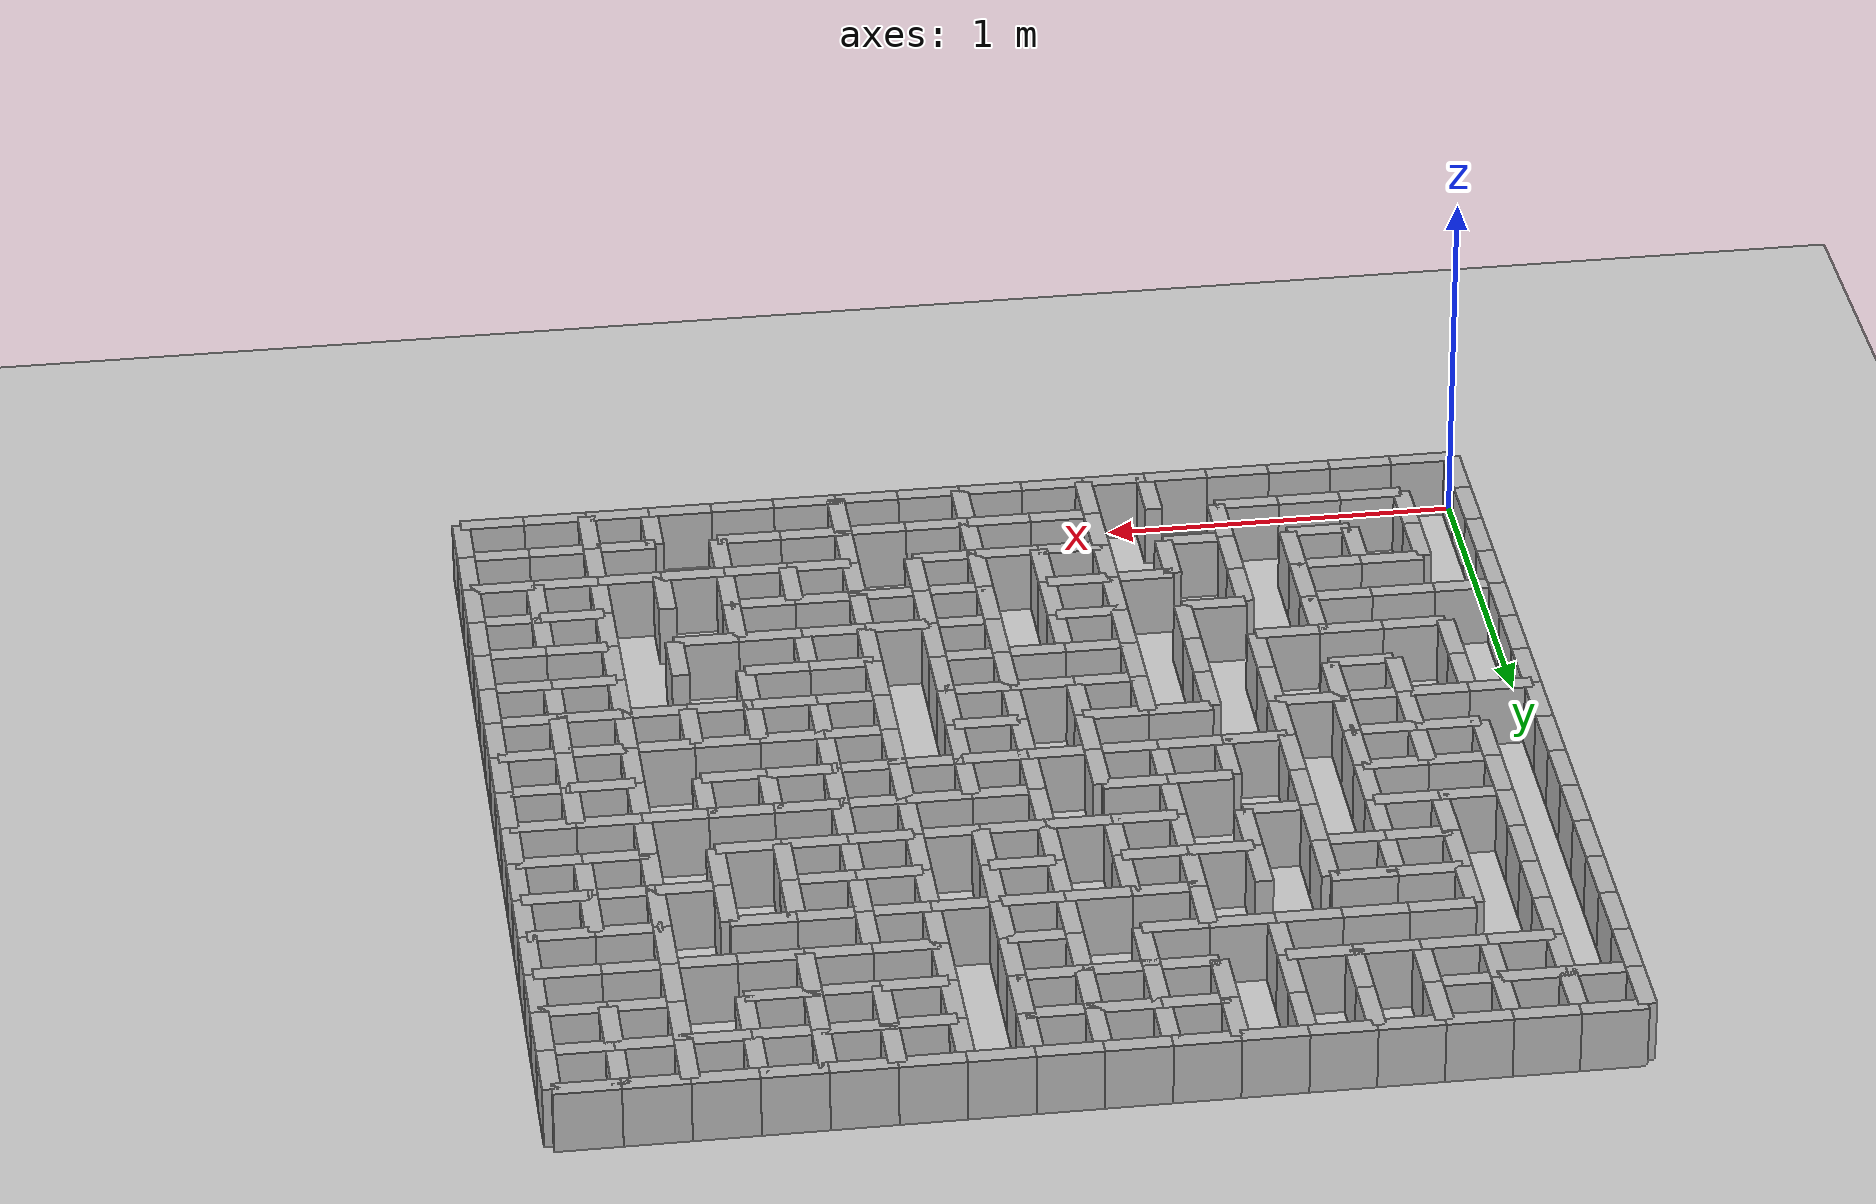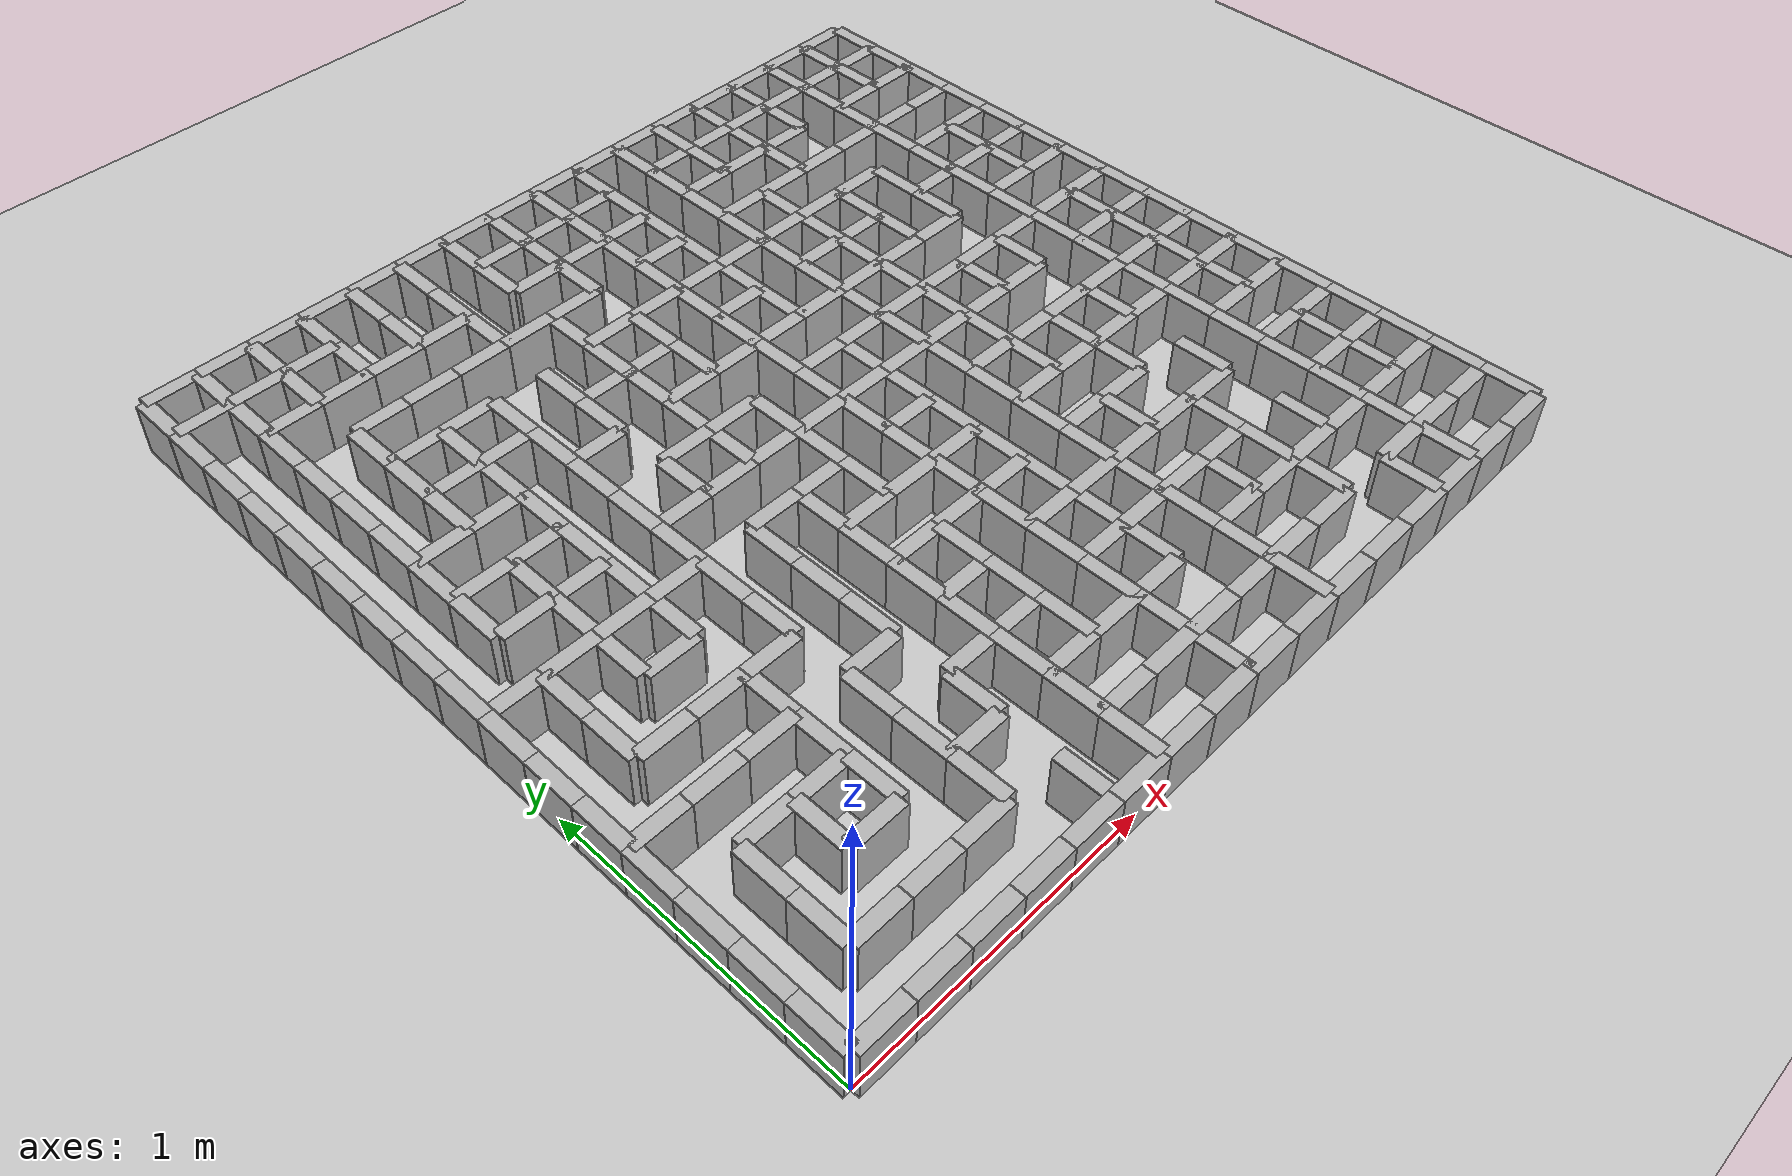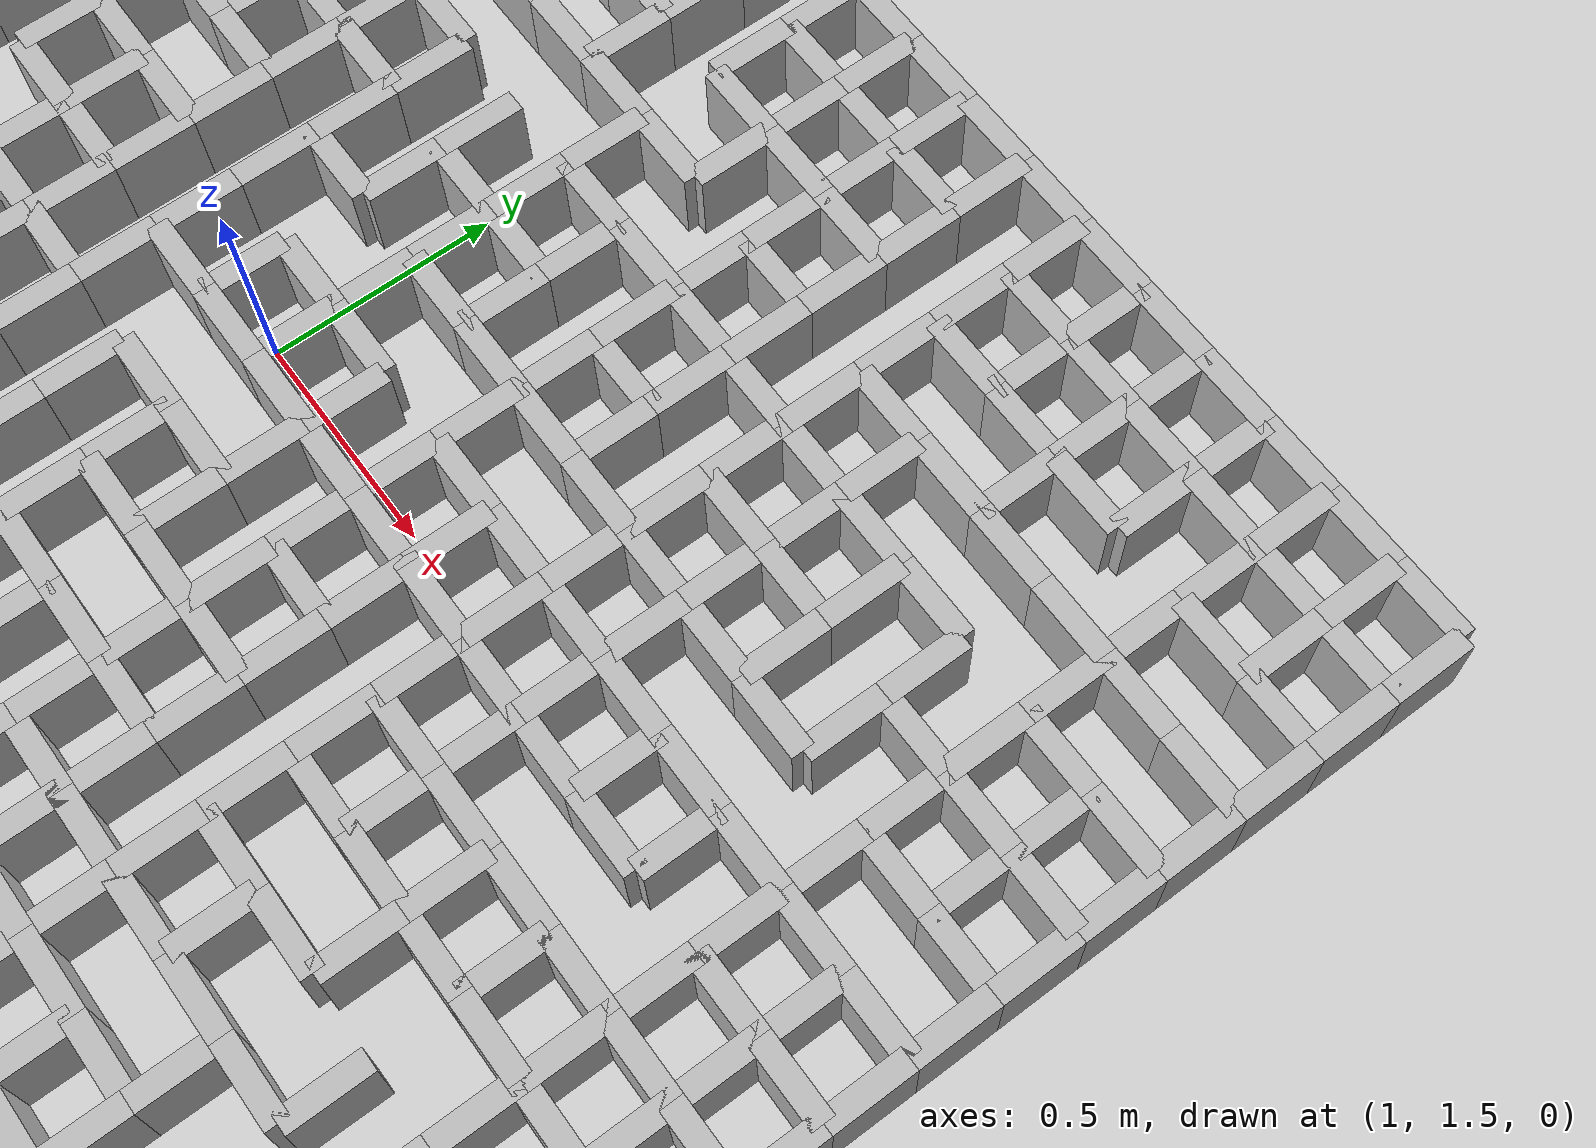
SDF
<sdf version="1.6">
 <world name="default">
  <light name="sun" type="directional">
   <pose>0 0 10 0 -0 0</pose>
   <diffuse>0.8 0.8 0.8 1</diffuse>
   <specular>0.2 0.2 0.2 1</specular>
   <attenuation>
    <range>1000</range>
    <constant>0.9</constant>
    <linear>0.01</linear>
    <quadratic>0.001</quadratic>
   </attenuation>
   <direction>-0.5 0.1 -0.9</direction>
  </light>
  <model name="ground_plane">
   <static>1</static>
   <link name="link">
    <collision name="collision">
     <geometry><plane><normal>0 0 1</normal><size>100 100</size></plane></geometry>
     <surface><friction><ode><mu>100</mu><mu2>50</mu2></ode></friction></surface>
    </collision>
    <visual name="visual">
     <cast_shadows>0</cast_shadows>
     <geometry><plane><normal>0 0 1</normal><size>100 100</size></plane></geometry>
     <material>
      <script><uri>file://media/materials/scripts/gazebo.material</uri><name>Gazebo/Grey</name></script>
     </material>
    </visual>
   </link>
  </model>
  <gravity>0 0 -9.8</gravity>
  <magnetic_field>6e-06 2.3e-05 -4.2e-05</magnetic_field>
  <atmosphere type="adiabatic"/>
  <physics name="default_physics" default="0" type="ode">
   <max_step_size>0.001</max_step_size>
   <real_time_factor>1</real_time_factor>
   <real_time_update_rate>1000</real_time_update_rate>
  </physics>
  <scene><ambient>0.4 0.4 0.4 1</ambient><background>0.7 0.7 0.7 1</background><shadows>1</shadows></scene>
  <audio><device>default</device></audio>
  <spherical_coordinates>
   <surface_model>EARTH_WGS84</surface_model>
   <latitude_deg>0</latitude_deg>
   <longitude_deg>0</longitude_deg>
   <elevation>0</elevation>
   <heading_deg>0</heading_deg>
  </spherical_coordinates>
  <model name="labyrinth_wall0">
   <pose>0.090000 0.000000 0.09 0 0 0.000000</pose>
   <link name="link">
    <inertial><mass>3.0</mass></inertial>
    <collision name="collision"><geometry><box><size>0.180 0.050 0.180</size></box></geometry></collision>
    <visual name="visual"><geometry><box><size>0.180 0.050 0.180</size></box></geometry></visual>
   </link>
   <static>true</static>
  </model>
  <model name="labyrinth_wall2">
   <pose>0.000000 0.090000 0.09 0 0 1.570796</pose>
   <link name="link">
    <inertial><mass>3.0</mass></inertial>
    <collision name="collision"><geometry><box><size>0.180 0.050 0.180</size></box></geometry></collision>
    <visual name="visual"><geometry><box><size>0.180 0.050 0.180</size></box></geometry></visual>
   </link>
   <static>true</static>
  </model>
  <model name="labyrinth_wall3">
   <pose>0.270000 0.000000 0.09 0 0 0.000000</pose>
   <link name="link">
    <inertial><mass>3.0</mass></inertial>
    <collision name="collision"><geometry><box><size>0.180 0.050 0.180</size></box></geometry></collision>
    <visual name="visual"><geometry><box><size>0.180 0.050 0.180</size></box></geometry></visual>
   </link>
   <static>true</static>
  </model>
  <model name="labyrinth_wall5">
   <pose>0.450000 0.000000 0.09 0 0 0.000000</pose>
   <link name="link">
    <inertial><mass>3.0</mass></inertial>
    <collision name="collision"><geometry><box><size>0.180 0.050 0.180</size></box></geometry></collision>
    <visual name="visual"><geometry><box><size>0.180 0.050 0.180</size></box></geometry></visual>
   </link>
   <static>true</static>
  </model>
  <model name="labyrinth_wall7">
   <pose>0.630000 0.000000 0.09 0 0 0.000000</pose>
   <link name="link">
    <inertial><mass>3.0</mass></inertial>
    <collision name="collision"><geometry><box><size>0.180 0.050 0.180</size></box></geometry></collision>
    <visual name="visual"><geometry><box><size>0.180 0.050 0.180</size></box></geometry></visual>
   </link>
   <static>true</static>
  </model>
  <model name="labyrinth_wall9">
   <pose>0.810000 0.000000 0.09 0 0 0.000000</pose>
   <link name="link">
    <inertial><mass>3.0</mass></inertial>
    <collision name="collision"><geometry><box><size>0.180 0.050 0.180</size></box></geometry></collision>
    <visual name="visual"><geometry><box><size>0.180 0.050 0.180</size></box></geometry></visual>
   </link>
   <static>true</static>
  </model>
  <model name="labyrinth_wall10">
   <pose>0.900000 0.090000 0.09 0 0 1.570796</pose>
   <link name="link">
    <inertial><mass>3.0</mass></inertial>
    <collision name="collision"><geometry><box><size>0.180 0.050 0.180</size></box></geometry></collision>
    <visual name="visual"><geometry><box><size>0.180 0.050 0.180</size></box></geometry></visual>
   </link>
   <static>true</static>
  </model>
  <model name="labyrinth_wall11">
   <pose>0.990000 0.000000 0.09 0 0 0.000000</pose>
   <link name="link">
    <inertial><mass>3.0</mass></inertial>
    <collision name="collision"><geometry><box><size>0.180 0.050 0.180</size></box></geometry></collision>
    <visual name="visual"><geometry><box><size>0.180 0.050 0.180</size></box></geometry></visual>
   </link>
   <static>true</static>
  </model>
  <model name="labyrinth_wall12">
   <pose>1.080000 0.090000 0.09 0 0 1.570796</pose>
   <link name="link">
    <inertial><mass>3.0</mass></inertial>
    <collision name="collision"><geometry><box><size>0.180 0.050 0.180</size></box></geometry></collision>
    <visual name="visual"><geometry><box><size>0.180 0.050 0.180</size></box></geometry></visual>
   </link>
   <static>true</static>
  </model>
  <model name="labyrinth_wall13">
   <pose>1.170000 0.000000 0.09 0 0 0.000000</pose>
   <link name="link">
    <inertial><mass>3.0</mass></inertial>
    <collision name="collision"><geometry><box><size>0.180 0.050 0.180</size></box></geometry></collision>
    <visual name="visual"><geometry><box><size>0.180 0.050 0.180</size></box></geometry></visual>
   </link>
   <static>true</static>
  </model>
  <model name="labyrinth_wall15">
   <pose>1.350000 0.000000 0.09 0 0 0.000000</pose>
   <link name="link">
    <inertial><mass>3.0</mass></inertial>
    <collision name="collision"><geometry><box><size>0.180 0.050 0.180</size></box></geometry></collision>
    <visual name="visual"><geometry><box><size>0.180 0.050 0.180</size></box></geometry></visual>
   </link>
   <static>true</static>
  </model>
  <model name="labyrinth_wall16">
   <pose>1.440000 0.090000 0.09 0 0 1.570796</pose>
   <link name="link">
    <inertial><mass>3.0</mass></inertial>
    <collision name="collision"><geometry><box><size>0.180 0.050 0.180</size></box></geometry></collision>
    <visual name="visual"><geometry><box><size>0.180 0.050 0.180</size></box></geometry></visual>
   </link>
   <static>true</static>
  </model>
  <model name="labyrinth_wall17">
   <pose>1.530000 0.000000 0.09 0 0 0.000000</pose>
   <link name="link">
    <inertial><mass>3.0</mass></inertial>
    <collision name="collision"><geometry><box><size>0.180 0.050 0.180</size></box></geometry></collision>
    <visual name="visual"><geometry><box><size>0.180 0.050 0.180</size></box></geometry></visual>
   </link>
   <static>true</static>
  </model>
  <model name="labyrinth_wall19">
   <pose>1.710000 0.000000 0.09 0 0 0.000000</pose>
   <link name="link">
    <inertial><mass>3.0</mass></inertial>
    <collision name="collision"><geometry><box><size>0.180 0.050 0.180</size></box></geometry></collision>
    <visual name="visual"><geometry><box><size>0.180 0.050 0.180</size></box></geometry></visual>
   </link>
   <static>true</static>
  </model>
  <model name="labyrinth_wall20">
   <pose>1.800000 0.090000 0.09 0 0 1.570796</pose>
   <link name="link">
    <inertial><mass>3.0</mass></inertial>
    <collision name="collision"><geometry><box><size>0.180 0.050 0.180</size></box></geometry></collision>
    <visual name="visual"><geometry><box><size>0.180 0.050 0.180</size></box></geometry></visual>
   </link>
   <static>true</static>
  </model>
  <model name="labyrinth_wall21">
   <pose>1.890000 0.000000 0.09 0 0 0.000000</pose>
   <link name="link">
    <inertial><mass>3.0</mass></inertial>
    <collision name="collision"><geometry><box><size>0.180 0.050 0.180</size></box></geometry></collision>
    <visual name="visual"><geometry><box><size>0.180 0.050 0.180</size></box></geometry></visual>
   </link>
   <static>true</static>
  </model>
  <model name="labyrinth_wall23">
   <pose>2.070000 0.000000 0.09 0 0 0.000000</pose>
   <link name="link">
    <inertial><mass>3.0</mass></inertial>
    <collision name="collision"><geometry><box><size>0.180 0.050 0.180</size></box></geometry></collision>
    <visual name="visual"><geometry><box><size>0.180 0.050 0.180</size></box></geometry></visual>
   </link>
   <static>true</static>
  </model>
  <model name="labyrinth_wall25">
   <pose>2.250000 0.000000 0.09 0 0 0.000000</pose>
   <link name="link">
    <inertial><mass>3.0</mass></inertial>
    <collision name="collision"><geometry><box><size>0.180 0.050 0.180</size></box></geometry></collision>
    <visual name="visual"><geometry><box><size>0.180 0.050 0.180</size></box></geometry></visual>
   </link>
   <static>true</static>
  </model>
  <model name="labyrinth_wall26">
   <pose>2.340000 0.090000 0.09 0 0 1.570796</pose>
   <link name="link">
    <inertial><mass>3.0</mass></inertial>
    <collision name="collision"><geometry><box><size>0.180 0.050 0.180</size></box></geometry></collision>
    <visual name="visual"><geometry><box><size>0.180 0.050 0.180</size></box></geometry></visual>
   </link>
   <static>true</static>
  </model>
  <model name="labyrinth_wall27">
   <pose>2.430000 0.000000 0.09 0 0 0.000000</pose>
   <link name="link">
    <inertial><mass>3.0</mass></inertial>
    <collision name="collision"><geometry><box><size>0.180 0.050 0.180</size></box></geometry></collision>
    <visual name="visual"><geometry><box><size>0.180 0.050 0.180</size></box></geometry></visual>
   </link>
   <static>true</static>
  </model>
  <model name="labyrinth_wall28">
   <pose>2.520000 0.090000 0.09 0 0 1.570796</pose>
   <link name="link">
    <inertial><mass>3.0</mass></inertial>
    <collision name="collision"><geometry><box><size>0.180 0.050 0.180</size></box></geometry></collision>
    <visual name="visual"><geometry><box><size>0.180 0.050 0.180</size></box></geometry></visual>
   </link>
   <static>true</static>
  </model>
  <model name="labyrinth_wall29">
   <pose>2.610000 0.000000 0.09 0 0 0.000000</pose>
   <link name="link">
    <inertial><mass>3.0</mass></inertial>
    <collision name="collision"><geometry><box><size>0.180 0.050 0.180</size></box></geometry></collision>
    <visual name="visual"><geometry><box><size>0.180 0.050 0.180</size></box></geometry></visual>
   </link>
   <static>true</static>
  </model>
  <model name="labyrinth_wall31">
   <pose>2.790000 0.000000 0.09 0 0 0.000000</pose>
   <link name="link">
    <inertial><mass>3.0</mass></inertial>
    <collision name="collision"><geometry><box><size>0.180 0.050 0.180</size></box></geometry></collision>
    <visual name="visual"><geometry><box><size>0.180 0.050 0.180</size></box></geometry></visual>
   </link>
   <static>true</static>
  </model>
  <model name="labyrinth_wall32">
   <pose>2.880000 0.090000 0.09 0 0 1.570796</pose>
   <link name="link">
    <inertial><mass>3.0</mass></inertial>
    <collision name="collision"><geometry><box><size>0.180 0.050 0.180</size></box></geometry></collision>
    <visual name="visual"><geometry><box><size>0.180 0.050 0.180</size></box></geometry></visual>
   </link>
   <static>true</static>
  </model>
  <model name="labyrinth_wall34">
   <pose>0.180000 0.270000 0.09 0 0 1.570796</pose>
   <link name="link">
    <inertial><mass>3.0</mass></inertial>
    <collision name="collision"><geometry><box><size>0.180 0.050 0.180</size></box></geometry></collision>
    <visual name="visual"><geometry><box><size>0.180 0.050 0.180</size></box></geometry></visual>
   </link>
   <static>true</static>
  </model>
  <model name="labyrinth_wall35">
   <pose>0.000000 0.270000 0.09 0 0 1.570796</pose>
   <link name="link">
    <inertial><mass>3.0</mass></inertial>
    <collision name="collision"><geometry><box><size>0.180 0.050 0.180</size></box></geometry></collision>
    <visual name="visual"><geometry><box><size>0.180 0.050 0.180</size></box></geometry></visual>
   </link>
   <static>true</static>
  </model>
  <model name="labyrinth_wall36">
   <pose>0.270000 0.180000 0.09 0 0 0.000000</pose>
   <link name="link">
    <inertial><mass>3.0</mass></inertial>
    <collision name="collision"><geometry><box><size>0.180 0.050 0.180</size></box></geometry></collision>
    <visual name="visual"><geometry><box><size>0.180 0.050 0.180</size></box></geometry></visual>
   </link>
   <static>true</static>
  </model>
  <model name="labyrinth_wall38">
   <pose>0.450000 0.180000 0.09 0 0 0.000000</pose>
   <link name="link">
    <inertial><mass>3.0</mass></inertial>
    <collision name="collision"><geometry><box><size>0.180 0.050 0.180</size></box></geometry></collision>
    <visual name="visual"><geometry><box><size>0.180 0.050 0.180</size></box></geometry></visual>
   </link>
   <static>true</static>
  </model>
  <model name="labyrinth_wall40">
   <pose>0.630000 0.180000 0.09 0 0 0.000000</pose>
   <link name="link">
    <inertial><mass>3.0</mass></inertial>
    <collision name="collision"><geometry><box><size>0.180 0.050 0.180</size></box></geometry></collision>
    <visual name="visual"><geometry><box><size>0.180 0.050 0.180</size></box></geometry></visual>
   </link>
   <static>true</static>
  </model>
  <model name="labyrinth_wall41">
   <pose>0.720000 0.270000 0.09 0 0 1.570796</pose>
   <link name="link">
    <inertial><mass>3.0</mass></inertial>
    <collision name="collision"><geometry><box><size>0.180 0.050 0.180</size></box></geometry></collision>
    <visual name="visual"><geometry><box><size>0.180 0.050 0.180</size></box></geometry></visual>
   </link>
   <static>true</static>
  </model>
  <model name="labyrinth_wall45">
   <pose>1.080000 0.270000 0.09 0 0 1.570796</pose>
   <link name="link">
    <inertial><mass>3.0</mass></inertial>
    <collision name="collision"><geometry><box><size>0.180 0.050 0.180</size></box></geometry></collision>
    <visual name="visual"><geometry><box><size>0.180 0.050 0.180</size></box></geometry></visual>
   </link>
   <static>true</static>
  </model>
  <model name="labyrinth_wall46">
   <pose>1.170000 0.180000 0.09 0 0 0.000000</pose>
   <link name="link">
    <inertial><mass>3.0</mass></inertial>
    <collision name="collision"><geometry><box><size>0.180 0.050 0.180</size></box></geometry></collision>
    <visual name="visual"><geometry><box><size>0.180 0.050 0.180</size></box></geometry></visual>
   </link>
   <static>true</static>
  </model>
  <model name="labyrinth_wall48">
   <pose>1.350000 0.180000 0.09 0 0 0.000000</pose>
   <link name="link">
    <inertial><mass>3.0</mass></inertial>
    <collision name="collision"><geometry><box><size>0.180 0.050 0.180</size></box></geometry></collision>
    <visual name="visual"><geometry><box><size>0.180 0.050 0.180</size></box></geometry></visual>
   </link>
   <static>true</static>
  </model>
  <model name="labyrinth_wall49">
   <pose>1.440000 0.270000 0.09 0 0 1.570796</pose>
   <link name="link">
    <inertial><mass>3.0</mass></inertial>
    <collision name="collision"><geometry><box><size>0.180 0.050 0.180</size></box></geometry></collision>
    <visual name="visual"><geometry><box><size>0.180 0.050 0.180</size></box></geometry></visual>
   </link>
   <static>true</static>
  </model>
  <model name="labyrinth_wall50">
   <pose>1.530000 0.180000 0.09 0 0 0.000000</pose>
   <link name="link">
    <inertial><mass>3.0</mass></inertial>
    <collision name="collision"><geometry><box><size>0.180 0.050 0.180</size></box></geometry></collision>
    <visual name="visual"><geometry><box><size>0.180 0.050 0.180</size></box></geometry></visual>
   </link>
   <static>true</static>
  </model>
  <model name="labyrinth_wall52">
   <pose>1.710000 0.180000 0.09 0 0 0.000000</pose>
   <link name="link">
    <inertial><mass>3.0</mass></inertial>
    <collision name="collision"><geometry><box><size>0.180 0.050 0.180</size></box></geometry></collision>
    <visual name="visual"><geometry><box><size>0.180 0.050 0.180</size></box></geometry></visual>
   </link>
   <static>true</static>
  </model>
  <model name="labyrinth_wall53">
   <pose>1.800000 0.270000 0.09 0 0 1.570796</pose>
   <link name="link">
    <inertial><mass>3.0</mass></inertial>
    <collision name="collision"><geometry><box><size>0.180 0.050 0.180</size></box></geometry></collision>
    <visual name="visual"><geometry><box><size>0.180 0.050 0.180</size></box></geometry></visual>
   </link>
   <static>true</static>
  </model>
  <model name="labyrinth_wall54">
   <pose>1.890000 0.180000 0.09 0 0 0.000000</pose>
   <link name="link">
    <inertial><mass>3.0</mass></inertial>
    <collision name="collision"><geometry><box><size>0.180 0.050 0.180</size></box></geometry></collision>
    <visual name="visual"><geometry><box><size>0.180 0.050 0.180</size></box></geometry></visual>
   </link>
   <static>true</static>
  </model>
  <model name="labyrinth_wall56">
   <pose>2.070000 0.180000 0.09 0 0 0.000000</pose>
   <link name="link">
    <inertial><mass>3.0</mass></inertial>
    <collision name="collision"><geometry><box><size>0.180 0.050 0.180</size></box></geometry></collision>
    <visual name="visual"><geometry><box><size>0.180 0.050 0.180</size></box></geometry></visual>
   </link>
   <static>true</static>
  </model>
  <model name="labyrinth_wall57">
   <pose>2.160000 0.270000 0.09 0 0 1.570796</pose>
   <link name="link">
    <inertial><mass>3.0</mass></inertial>
    <collision name="collision"><geometry><box><size>0.180 0.050 0.180</size></box></geometry></collision>
    <visual name="visual"><geometry><box><size>0.180 0.050 0.180</size></box></geometry></visual>
   </link>
   <static>true</static>
  </model>
  <model name="labyrinth_wall60">
   <pose>2.430000 0.180000 0.09 0 0 0.000000</pose>
   <link name="link">
    <inertial><mass>3.0</mass></inertial>
    <collision name="collision"><geometry><box><size>0.180 0.050 0.180</size></box></geometry></collision>
    <visual name="visual"><geometry><box><size>0.180 0.050 0.180</size></box></geometry></visual>
   </link>
   <static>true</static>
  </model>
  <model name="labyrinth_wall61">
   <pose>2.520000 0.270000 0.09 0 0 1.570796</pose>
   <link name="link">
    <inertial><mass>3.0</mass></inertial>
    <collision name="collision"><geometry><box><size>0.180 0.050 0.180</size></box></geometry></collision>
    <visual name="visual"><geometry><box><size>0.180 0.050 0.180</size></box></geometry></visual>
   </link>
   <static>true</static>
  </model>
  <model name="labyrinth_wall62">
   <pose>2.610000 0.180000 0.09 0 0 0.000000</pose>
   <link name="link">
    <inertial><mass>3.0</mass></inertial>
    <collision name="collision"><geometry><box><size>0.180 0.050 0.180</size></box></geometry></collision>
    <visual name="visual"><geometry><box><size>0.180 0.050 0.180</size></box></geometry></visual>
   </link>
   <static>true</static>
  </model>
  <model name="labyrinth_wall64">
   <pose>2.790000 0.180000 0.09 0 0 0.000000</pose>
   <link name="link">
    <inertial><mass>3.0</mass></inertial>
    <collision name="collision"><geometry><box><size>0.180 0.050 0.180</size></box></geometry></collision>
    <visual name="visual"><geometry><box><size>0.180 0.050 0.180</size></box></geometry></visual>
   </link>
   <static>true</static>
  </model>
  <model name="labyrinth_wall65">
   <pose>2.880000 0.270000 0.09 0 0 1.570796</pose>
   <link name="link">
    <inertial><mass>3.0</mass></inertial>
    <collision name="collision"><geometry><box><size>0.180 0.050 0.180</size></box></geometry></collision>
    <visual name="visual"><geometry><box><size>0.180 0.050 0.180</size></box></geometry></visual>
   </link>
   <static>true</static>
  </model>
  <model name="labyrinth_wall67">
   <pose>0.180000 0.450000 0.09 0 0 1.570796</pose>
   <link name="link">
    <inertial><mass>3.0</mass></inertial>
    <collision name="collision"><geometry><box><size>0.180 0.050 0.180</size></box></geometry></collision>
    <visual name="visual"><geometry><box><size>0.180 0.050 0.180</size></box></geometry></visual>
   </link>
   <static>true</static>
  </model>
  <model name="labyrinth_wall68">
   <pose>0.000000 0.450000 0.09 0 0 1.570796</pose>
   <link name="link">
    <inertial><mass>3.0</mass></inertial>
    <collision name="collision"><geometry><box><size>0.180 0.050 0.180</size></box></geometry></collision>
    <visual name="visual"><geometry><box><size>0.180 0.050 0.180</size></box></geometry></visual>
   </link>
   <static>true</static>
  </model>
  <model name="labyrinth_wall70">
   <pose>0.360000 0.450000 0.09 0 0 1.570796</pose>
   <link name="link">
    <inertial><mass>3.0</mass></inertial>
    <collision name="collision"><geometry><box><size>0.180 0.050 0.180</size></box></geometry></collision>
    <visual name="visual"><geometry><box><size>0.180 0.050 0.180</size></box></geometry></visual>
   </link>
   <static>true</static>
  </model>
  <model name="labyrinth_wall71">
   <pose>0.450000 0.360000 0.09 0 0 0.000000</pose>
   <link name="link">
    <inertial><mass>3.0</mass></inertial>
    <collision name="collision"><geometry><box><size>0.180 0.050 0.180</size></box></geometry></collision>
    <visual name="visual"><geometry><box><size>0.180 0.050 0.180</size></box></geometry></visual>
   </link>
   <static>true</static>
  </model>
  <model name="labyrinth_wall72">
   <pose>0.540000 0.450000 0.09 0 0 1.570796</pose>
   <link name="link">
    <inertial><mass>3.0</mass></inertial>
    <collision name="collision"><geometry><box><size>0.180 0.050 0.180</size></box></geometry></collision>
    <visual name="visual"><geometry><box><size>0.180 0.050 0.180</size></box></geometry></visual>
   </link>
   <static>true</static>
  </model>
  <model name="labyrinth_wall74">
   <pose>0.720000 0.450000 0.09 0 0 1.570796</pose>
   <link name="link">
    <inertial><mass>3.0</mass></inertial>
    <collision name="collision"><geometry><box><size>0.180 0.050 0.180</size></box></geometry></collision>
    <visual name="visual"><geometry><box><size>0.180 0.050 0.180</size></box></geometry></visual>
   </link>
   <static>true</static>
  </model>
  <model name="labyrinth_wall75">
   <pose>0.810000 0.360000 0.09 0 0 0.000000</pose>
   <link name="link">
    <inertial><mass>3.0</mass></inertial>
    <collision name="collision"><geometry><box><size>0.180 0.050 0.180</size></box></geometry></collision>
    <visual name="visual"><geometry><box><size>0.180 0.050 0.180</size></box></geometry></visual>
   </link>
   <static>true</static>
  </model>
  <model name="labyrinth_wall76">
   <pose>0.900000 0.450000 0.09 0 0 1.570796</pose>
   <link name="link">
    <inertial><mass>3.0</mass></inertial>
    <collision name="collision"><geometry><box><size>0.180 0.050 0.180</size></box></geometry></collision>
    <visual name="visual"><geometry><box><size>0.180 0.050 0.180</size></box></geometry></visual>
   </link>
   <static>true</static>
  </model>
  <model name="labyrinth_wall78">
   <pose>1.080000 0.450000 0.09 0 0 1.570796</pose>
   <link name="link">
    <inertial><mass>3.0</mass></inertial>
    <collision name="collision"><geometry><box><size>0.180 0.050 0.180</size></box></geometry></collision>
    <visual name="visual"><geometry><box><size>0.180 0.050 0.180</size></box></geometry></visual>
   </link>
   <static>true</static>
  </model>
  <model name="labyrinth_wall79">
   <pose>1.170000 0.360000 0.09 0 0 0.000000</pose>
   <link name="link">
    <inertial><mass>3.0</mass></inertial>
    <collision name="collision"><geometry><box><size>0.180 0.050 0.180</size></box></geometry></collision>
    <visual name="visual"><geometry><box><size>0.180 0.050 0.180</size></box></geometry></visual>
   </link>
   <static>true</static>
  </model>
  <model name="labyrinth_wall80">
   <pose>1.260000 0.450000 0.09 0 0 1.570796</pose>
   <link name="link">
    <inertial><mass>3.0</mass></inertial>
    <collision name="collision"><geometry><box><size>0.180 0.050 0.180</size></box></geometry></collision>
    <visual name="visual"><geometry><box><size>0.180 0.050 0.180</size></box></geometry></visual>
   </link>
   <static>true</static>
  </model>
  <model name="labyrinth_wall81">
   <pose>1.350000 0.360000 0.09 0 0 0.000000</pose>
   <link name="link">
    <inertial><mass>3.0</mass></inertial>
    <collision name="collision"><geometry><box><size>0.180 0.050 0.180</size></box></geometry></collision>
    <visual name="visual"><geometry><box><size>0.180 0.050 0.180</size></box></geometry></visual>
   </link>
   <static>true</static>
  </model>
  <model name="labyrinth_wall82">
   <pose>1.440000 0.450000 0.09 0 0 1.570796</pose>
   <link name="link">
    <inertial><mass>3.0</mass></inertial>
    <collision name="collision"><geometry><box><size>0.180 0.050 0.180</size></box></geometry></collision>
    <visual name="visual"><geometry><box><size>0.180 0.050 0.180</size></box></geometry></visual>
   </link>
   <static>true</static>
  </model>
  <model name="labyrinth_wall83">
   <pose>1.530000 0.360000 0.09 0 0 0.000000</pose>
   <link name="link">
    <inertial><mass>3.0</mass></inertial>
    <collision name="collision"><geometry><box><size>0.180 0.050 0.180</size></box></geometry></collision>
    <visual name="visual"><geometry><box><size>0.180 0.050 0.180</size></box></geometry></visual>
   </link>
   <static>true</static>
  </model>
  <model name="labyrinth_wall84">
   <pose>1.620000 0.450000 0.09 0 0 1.570796</pose>
   <link name="link">
    <inertial><mass>3.0</mass></inertial>
    <collision name="collision"><geometry><box><size>0.180 0.050 0.180</size></box></geometry></collision>
    <visual name="visual"><geometry><box><size>0.180 0.050 0.180</size></box></geometry></visual>
   </link>
   <static>true</static>
  </model>
  <model name="labyrinth_wall86">
   <pose>1.800000 0.450000 0.09 0 0 1.570796</pose>
   <link name="link">
    <inertial><mass>3.0</mass></inertial>
    <collision name="collision"><geometry><box><size>0.180 0.050 0.180</size></box></geometry></collision>
    <visual name="visual"><geometry><box><size>0.180 0.050 0.180</size></box></geometry></visual>
   </link>
   <static>true</static>
  </model>
  <model name="labyrinth_wall87">
   <pose>1.890000 0.360000 0.09 0 0 0.000000</pose>
   <link name="link">
    <inertial><mass>3.0</mass></inertial>
    <collision name="collision"><geometry><box><size>0.180 0.050 0.180</size></box></geometry></collision>
    <visual name="visual"><geometry><box><size>0.180 0.050 0.180</size></box></geometry></visual>
   </link>
   <static>true</static>
  </model>
  <model name="labyrinth_wall88">
   <pose>1.980000 0.450000 0.09 0 0 1.570796</pose>
   <link name="link">
    <inertial><mass>3.0</mass></inertial>
    <collision name="collision"><geometry><box><size>0.180 0.050 0.180</size></box></geometry></collision>
    <visual name="visual"><geometry><box><size>0.180 0.050 0.180</size></box></geometry></visual>
   </link>
   <static>true</static>
  </model>
  <model name="labyrinth_wall89">
   <pose>2.070000 0.360000 0.09 0 0 0.000000</pose>
   <link name="link">
    <inertial><mass>3.0</mass></inertial>
    <collision name="collision"><geometry><box><size>0.180 0.050 0.180</size></box></geometry></collision>
    <visual name="visual"><geometry><box><size>0.180 0.050 0.180</size></box></geometry></visual>
   </link>
   <static>true</static>
  </model>
  <model name="labyrinth_wall90">
   <pose>2.160000 0.450000 0.09 0 0 1.570796</pose>
   <link name="link">
    <inertial><mass>3.0</mass></inertial>
    <collision name="collision"><geometry><box><size>0.180 0.050 0.180</size></box></geometry></collision>
    <visual name="visual"><geometry><box><size>0.180 0.050 0.180</size></box></geometry></visual>
   </link>
   <static>true</static>
  </model>
  <model name="labyrinth_wall91">
   <pose>2.250000 0.360000 0.09 0 0 0.000000</pose>
   <link name="link">
    <inertial><mass>3.0</mass></inertial>
    <collision name="collision"><geometry><box><size>0.180 0.050 0.180</size></box></geometry></collision>
    <visual name="visual"><geometry><box><size>0.180 0.050 0.180</size></box></geometry></visual>
   </link>
   <static>true</static>
  </model>
  <model name="labyrinth_wall92">
   <pose>2.340000 0.450000 0.09 0 0 1.570796</pose>
   <link name="link">
    <inertial><mass>3.0</mass></inertial>
    <collision name="collision"><geometry><box><size>0.180 0.050 0.180</size></box></geometry></collision>
    <visual name="visual"><geometry><box><size>0.180 0.050 0.180</size></box></geometry></visual>
   </link>
   <static>true</static>
  </model>
  <model name="labyrinth_wall93">
   <pose>2.430000 0.360000 0.09 0 0 0.000000</pose>
   <link name="link">
    <inertial><mass>3.0</mass></inertial>
    <collision name="collision"><geometry><box><size>0.180 0.050 0.180</size></box></geometry></collision>
    <visual name="visual"><geometry><box><size>0.180 0.050 0.180</size></box></geometry></visual>
   </link>
   <static>true</static>
  </model>
  <model name="labyrinth_wall94">
   <pose>2.520000 0.450000 0.09 0 0 1.570796</pose>
   <link name="link">
    <inertial><mass>3.0</mass></inertial>
    <collision name="collision"><geometry><box><size>0.180 0.050 0.180</size></box></geometry></collision>
    <visual name="visual"><geometry><box><size>0.180 0.050 0.180</size></box></geometry></visual>
   </link>
   <static>true</static>
  </model>
  <model name="labyrinth_wall95">
   <pose>2.610000 0.360000 0.09 0 0 0.000000</pose>
   <link name="link">
    <inertial><mass>3.0</mass></inertial>
    <collision name="collision"><geometry><box><size>0.180 0.050 0.180</size></box></geometry></collision>
    <visual name="visual"><geometry><box><size>0.180 0.050 0.180</size></box></geometry></visual>
   </link>
   <static>true</static>
  </model>
  <model name="labyrinth_wall96">
   <pose>2.700000 0.450000 0.09 0 0 1.570796</pose>
   <link name="link">
    <inertial><mass>3.0</mass></inertial>
    <collision name="collision"><geometry><box><size>0.180 0.050 0.180</size></box></geometry></collision>
    <visual name="visual"><geometry><box><size>0.180 0.050 0.180</size></box></geometry></visual>
   </link>
   <static>true</static>
  </model>
  <model name="labyrinth_wall97">
   <pose>2.790000 0.360000 0.09 0 0 0.000000</pose>
   <link name="link">
    <inertial><mass>3.0</mass></inertial>
    <collision name="collision"><geometry><box><size>0.180 0.050 0.180</size></box></geometry></collision>
    <visual name="visual"><geometry><box><size>0.180 0.050 0.180</size></box></geometry></visual>
   </link>
   <static>true</static>
  </model>
  <model name="labyrinth_wall98">
   <pose>2.880000 0.450000 0.09 0 0 1.570796</pose>
   <link name="link">
    <inertial><mass>3.0</mass></inertial>
    <collision name="collision"><geometry><box><size>0.180 0.050 0.180</size></box></geometry></collision>
    <visual name="visual"><geometry><box><size>0.180 0.050 0.180</size></box></geometry></visual>
   </link>
   <static>true</static>
  </model>
  <model name="labyrinth_wall101">
   <pose>0.000000 0.630000 0.09 0 0 1.570796</pose>
   <link name="link">
    <inertial><mass>3.0</mass></inertial>
    <collision name="collision"><geometry><box><size>0.180 0.050 0.180</size></box></geometry></collision>
    <visual name="visual"><geometry><box><size>0.180 0.050 0.180</size></box></geometry></visual>
   </link>
   <static>true</static>
  </model>
  <model name="labyrinth_wall102">
   <pose>0.270000 0.540000 0.09 0 0 0.000000</pose>
   <link name="link">
    <inertial><mass>3.0</mass></inertial>
    <collision name="collision"><geometry><box><size>0.180 0.050 0.180</size></box></geometry></collision>
    <visual name="visual"><geometry><box><size>0.180 0.050 0.180</size></box></geometry></visual>
   </link>
   <static>true</static>
  </model>
  <model name="labyrinth_wall104">
   <pose>0.450000 0.540000 0.09 0 0 0.000000</pose>
   <link name="link">
    <inertial><mass>3.0</mass></inertial>
    <collision name="collision"><geometry><box><size>0.180 0.050 0.180</size></box></geometry></collision>
    <visual name="visual"><geometry><box><size>0.180 0.050 0.180</size></box></geometry></visual>
   </link>
   <static>true</static>
  </model>
  <model name="labyrinth_wall105">
   <pose>0.540000 0.630000 0.09 0 0 1.570796</pose>
   <link name="link">
    <inertial><mass>3.0</mass></inertial>
    <collision name="collision"><geometry><box><size>0.180 0.050 0.180</size></box></geometry></collision>
    <visual name="visual"><geometry><box><size>0.180 0.050 0.180</size></box></geometry></visual>
   </link>
   <static>true</static>
  </model>
  <model name="labyrinth_wall107">
   <pose>0.720000 0.630000 0.09 0 0 1.570796</pose>
   <link name="link">
    <inertial><mass>3.0</mass></inertial>
    <collision name="collision"><geometry><box><size>0.180 0.050 0.180</size></box></geometry></collision>
    <visual name="visual"><geometry><box><size>0.180 0.050 0.180</size></box></geometry></visual>
   </link>
   <static>true</static>
  </model>
  <model name="labyrinth_wall110">
   <pose>0.990000 0.540000 0.09 0 0 0.000000</pose>
   <link name="link">
    <inertial><mass>3.0</mass></inertial>
    <collision name="collision"><geometry><box><size>0.180 0.050 0.180</size></box></geometry></collision>
    <visual name="visual"><geometry><box><size>0.180 0.050 0.180</size></box></geometry></visual>
   </link>
   <static>true</static>
  </model>
  <model name="labyrinth_wall111">
   <pose>1.080000 0.630000 0.09 0 0 1.570796</pose>
   <link name="link">
    <inertial><mass>3.0</mass></inertial>
    <collision name="collision"><geometry><box><size>0.180 0.050 0.180</size></box></geometry></collision>
    <visual name="visual"><geometry><box><size>0.180 0.050 0.180</size></box></geometry></visual>
   </link>
   <static>true</static>
  </model>
  <model name="labyrinth_wall112">
   <pose>1.170000 0.540000 0.09 0 0 0.000000</pose>
   <link name="link">
    <inertial><mass>3.0</mass></inertial>
    <collision name="collision"><geometry><box><size>0.180 0.050 0.180</size></box></geometry></collision>
    <visual name="visual"><geometry><box><size>0.180 0.050 0.180</size></box></geometry></visual>
   </link>
   <static>true</static>
  </model>
  <model name="labyrinth_wall113">
   <pose>1.260000 0.630000 0.09 0 0 1.570796</pose>
   <link name="link">
    <inertial><mass>3.0</mass></inertial>
    <collision name="collision"><geometry><box><size>0.180 0.050 0.180</size></box></geometry></collision>
    <visual name="visual"><geometry><box><size>0.180 0.050 0.180</size></box></geometry></visual>
   </link>
   <static>true</static>
  </model>
  <model name="labyrinth_wall115">
   <pose>1.440000 0.630000 0.09 0 0 1.570796</pose>
   <link name="link">
    <inertial><mass>3.0</mass></inertial>
    <collision name="collision"><geometry><box><size>0.180 0.050 0.180</size></box></geometry></collision>
    <visual name="visual"><geometry><box><size>0.180 0.050 0.180</size></box></geometry></visual>
   </link>
   <static>true</static>
  </model>
  <model name="labyrinth_wall116">
   <pose>1.530000 0.540000 0.09 0 0 0.000000</pose>
   <link name="link">
    <inertial><mass>3.0</mass></inertial>
    <collision name="collision"><geometry><box><size>0.180 0.050 0.180</size></box></geometry></collision>
    <visual name="visual"><geometry><box><size>0.180 0.050 0.180</size></box></geometry></visual>
   </link>
   <static>true</static>
  </model>
  <model name="labyrinth_wall117">
   <pose>1.620000 0.630000 0.09 0 0 1.570796</pose>
   <link name="link">
    <inertial><mass>3.0</mass></inertial>
    <collision name="collision"><geometry><box><size>0.180 0.050 0.180</size></box></geometry></collision>
    <visual name="visual"><geometry><box><size>0.180 0.050 0.180</size></box></geometry></visual>
   </link>
   <static>true</static>
  </model>
  <model name="labyrinth_wall118">
   <pose>1.710000 0.540000 0.09 0 0 0.000000</pose>
   <link name="link">
    <inertial><mass>3.0</mass></inertial>
    <collision name="collision"><geometry><box><size>0.180 0.050 0.180</size></box></geometry></collision>
    <visual name="visual"><geometry><box><size>0.180 0.050 0.180</size></box></geometry></visual>
   </link>
   <static>true</static>
  </model>
  <model name="labyrinth_wall119">
   <pose>1.800000 0.630000 0.09 0 0 1.570796</pose>
   <link name="link">
    <inertial><mass>3.0</mass></inertial>
    <collision name="collision"><geometry><box><size>0.180 0.050 0.180</size></box></geometry></collision>
    <visual name="visual"><geometry><box><size>0.180 0.050 0.180</size></box></geometry></visual>
   </link>
   <static>true</static>
  </model>
  <model name="labyrinth_wall120">
   <pose>1.890000 0.540000 0.09 0 0 0.000000</pose>
   <link name="link">
    <inertial><mass>3.0</mass></inertial>
    <collision name="collision"><geometry><box><size>0.180 0.050 0.180</size></box></geometry></collision>
    <visual name="visual"><geometry><box><size>0.180 0.050 0.180</size></box></geometry></visual>
   </link>
   <static>true</static>
  </model>
  <model name="labyrinth_wall122">
   <pose>2.070000 0.540000 0.09 0 0 0.000000</pose>
   <link name="link">
    <inertial><mass>3.0</mass></inertial>
    <collision name="collision"><geometry><box><size>0.180 0.050 0.180</size></box></geometry></collision>
    <visual name="visual"><geometry><box><size>0.180 0.050 0.180</size></box></geometry></visual>
   </link>
   <static>true</static>
  </model>
  <model name="labyrinth_wall123">
   <pose>2.160000 0.630000 0.09 0 0 1.570796</pose>
   <link name="link">
    <inertial><mass>3.0</mass></inertial>
    <collision name="collision"><geometry><box><size>0.180 0.050 0.180</size></box></geometry></collision>
    <visual name="visual"><geometry><box><size>0.180 0.050 0.180</size></box></geometry></visual>
   </link>
   <static>true</static>
  </model>
  <model name="labyrinth_wall127">
   <pose>2.520000 0.630000 0.09 0 0 1.570796</pose>
   <link name="link">
    <inertial><mass>3.0</mass></inertial>
    <collision name="collision"><geometry><box><size>0.180 0.050 0.180</size></box></geometry></collision>
    <visual name="visual"><geometry><box><size>0.180 0.050 0.180</size></box></geometry></visual>
   </link>
   <static>true</static>
  </model>
  <model name="labyrinth_wall128">
   <pose>2.610000 0.540000 0.09 0 0 0.000000</pose>
   <link name="link">
    <inertial><mass>3.0</mass></inertial>
    <collision name="collision"><geometry><box><size>0.180 0.050 0.180</size></box></geometry></collision>
    <visual name="visual"><geometry><box><size>0.180 0.050 0.180</size></box></geometry></visual>
   </link>
   <static>true</static>
  </model>
  <model name="labyrinth_wall129">
   <pose>2.700000 0.630000 0.09 0 0 1.570796</pose>
   <link name="link">
    <inertial><mass>3.0</mass></inertial>
    <collision name="collision"><geometry><box><size>0.180 0.050 0.180</size></box></geometry></collision>
    <visual name="visual"><geometry><box><size>0.180 0.050 0.180</size></box></geometry></visual>
   </link>
   <static>true</static>
  </model>
  <model name="labyrinth_wall130">
   <pose>2.790000 0.540000 0.09 0 0 0.000000</pose>
   <link name="link">
    <inertial><mass>3.0</mass></inertial>
    <collision name="collision"><geometry><box><size>0.180 0.050 0.180</size></box></geometry></collision>
    <visual name="visual"><geometry><box><size>0.180 0.050 0.180</size></box></geometry></visual>
   </link>
   <static>true</static>
  </model>
  <model name="labyrinth_wall131">
   <pose>2.880000 0.630000 0.09 0 0 1.570796</pose>
   <link name="link">
    <inertial><mass>3.0</mass></inertial>
    <collision name="collision"><geometry><box><size>0.180 0.050 0.180</size></box></geometry></collision>
    <visual name="visual"><geometry><box><size>0.180 0.050 0.180</size></box></geometry></visual>
   </link>
   <static>true</static>
  </model>
  <model name="labyrinth_wall132">
   <pose>0.090000 0.720000 0.09 0 0 0.000000</pose>
   <link name="link">
    <inertial><mass>3.0</mass></inertial>
    <collision name="collision"><geometry><box><size>0.180 0.050 0.180</size></box></geometry></collision>
    <visual name="visual"><geometry><box><size>0.180 0.050 0.180</size></box></geometry></visual>
   </link>
   <static>true</static>
  </model>
  <model name="labyrinth_wall134">
   <pose>0.000000 0.810000 0.09 0 0 1.570796</pose>
   <link name="link">
    <inertial><mass>3.0</mass></inertial>
    <collision name="collision"><geometry><box><size>0.180 0.050 0.180</size></box></geometry></collision>
    <visual name="visual"><geometry><box><size>0.180 0.050 0.180</size></box></geometry></visual>
   </link>
   <static>true</static>
  </model>
  <model name="labyrinth_wall135">
   <pose>0.270000 0.720000 0.09 0 0 0.000000</pose>
   <link name="link">
    <inertial><mass>3.0</mass></inertial>
    <collision name="collision"><geometry><box><size>0.180 0.050 0.180</size></box></geometry></collision>
    <visual name="visual"><geometry><box><size>0.180 0.050 0.180</size></box></geometry></visual>
   </link>
   <static>true</static>
  </model>
  <model name="labyrinth_wall137">
   <pose>0.450000 0.720000 0.09 0 0 0.000000</pose>
   <link name="link">
    <inertial><mass>3.0</mass></inertial>
    <collision name="collision"><geometry><box><size>0.180 0.050 0.180</size></box></geometry></collision>
    <visual name="visual"><geometry><box><size>0.180 0.050 0.180</size></box></geometry></visual>
   </link>
   <static>true</static>
  </model>
  <model name="labyrinth_wall138">
   <pose>0.540000 0.810000 0.09 0 0 1.570796</pose>
   <link name="link">
    <inertial><mass>3.0</mass></inertial>
    <collision name="collision"><geometry><box><size>0.180 0.050 0.180</size></box></geometry></collision>
    <visual name="visual"><geometry><box><size>0.180 0.050 0.180</size></box></geometry></visual>
   </link>
   <static>true</static>
  </model>
  <model name="labyrinth_wall141">
   <pose>0.810000 0.720000 0.09 0 0 0.000000</pose>
   <link name="link">
    <inertial><mass>3.0</mass></inertial>
    <collision name="collision"><geometry><box><size>0.180 0.050 0.180</size></box></geometry></collision>
    <visual name="visual"><geometry><box><size>0.180 0.050 0.180</size></box></geometry></visual>
   </link>
   <static>true</static>
  </model>
  <model name="labyrinth_wall142">
   <pose>0.900000 0.810000 0.09 0 0 1.570796</pose>
   <link name="link">
    <inertial><mass>3.0</mass></inertial>
    <collision name="collision"><geometry><box><size>0.180 0.050 0.180</size></box></geometry></collision>
    <visual name="visual"><geometry><box><size>0.180 0.050 0.180</size></box></geometry></visual>
   </link>
   <static>true</static>
  </model>
  <model name="labyrinth_wall144">
   <pose>1.080000 0.810000 0.09 0 0 1.570796</pose>
   <link name="link">
    <inertial><mass>3.0</mass></inertial>
    <collision name="collision"><geometry><box><size>0.180 0.050 0.180</size></box></geometry></collision>
    <visual name="visual"><geometry><box><size>0.180 0.050 0.180</size></box></geometry></visual>
   </link>
   <static>true</static>
  </model>
  <model name="labyrinth_wall145">
   <pose>1.170000 0.720000 0.09 0 0 0.000000</pose>
   <link name="link">
    <inertial><mass>3.0</mass></inertial>
    <collision name="collision"><geometry><box><size>0.180 0.050 0.180</size></box></geometry></collision>
    <visual name="visual"><geometry><box><size>0.180 0.050 0.180</size></box></geometry></visual>
   </link>
   <static>true</static>
  </model>
  <model name="labyrinth_wall146">
   <pose>1.260000 0.810000 0.09 0 0 1.570796</pose>
   <link name="link">
    <inertial><mass>3.0</mass></inertial>
    <collision name="collision"><geometry><box><size>0.180 0.050 0.180</size></box></geometry></collision>
    <visual name="visual"><geometry><box><size>0.180 0.050 0.180</size></box></geometry></visual>
   </link>
   <static>true</static>
  </model>
  <model name="labyrinth_wall148">
   <pose>1.440000 0.810000 0.09 0 0 1.570796</pose>
   <link name="link">
    <inertial><mass>3.0</mass></inertial>
    <collision name="collision"><geometry><box><size>0.180 0.050 0.180</size></box></geometry></collision>
    <visual name="visual"><geometry><box><size>0.180 0.050 0.180</size></box></geometry></visual>
   </link>
   <static>true</static>
  </model>
  <model name="labyrinth_wall149">
   <pose>1.530000 0.720000 0.09 0 0 0.000000</pose>
   <link name="link">
    <inertial><mass>3.0</mass></inertial>
    <collision name="collision"><geometry><box><size>0.180 0.050 0.180</size></box></geometry></collision>
    <visual name="visual"><geometry><box><size>0.180 0.050 0.180</size></box></geometry></visual>
   </link>
   <static>true</static>
  </model>
  <model name="labyrinth_wall150">
   <pose>1.620000 0.810000 0.09 0 0 1.570796</pose>
   <link name="link">
    <inertial><mass>3.0</mass></inertial>
    <collision name="collision"><geometry><box><size>0.180 0.050 0.180</size></box></geometry></collision>
    <visual name="visual"><geometry><box><size>0.180 0.050 0.180</size></box></geometry></visual>
   </link>
   <static>true</static>
  </model>
  <model name="labyrinth_wall151">
   <pose>1.710000 0.720000 0.09 0 0 0.000000</pose>
   <link name="link">
    <inertial><mass>3.0</mass></inertial>
    <collision name="collision"><geometry><box><size>0.180 0.050 0.180</size></box></geometry></collision>
    <visual name="visual"><geometry><box><size>0.180 0.050 0.180</size></box></geometry></visual>
   </link>
   <static>true</static>
  </model>
  <model name="labyrinth_wall152">
   <pose>1.800000 0.810000 0.09 0 0 1.570796</pose>
   <link name="link">
    <inertial><mass>3.0</mass></inertial>
    <collision name="collision"><geometry><box><size>0.180 0.050 0.180</size></box></geometry></collision>
    <visual name="visual"><geometry><box><size>0.180 0.050 0.180</size></box></geometry></visual>
   </link>
   <static>true</static>
  </model>
  <model name="labyrinth_wall153">
   <pose>1.890000 0.720000 0.09 0 0 0.000000</pose>
   <link name="link">
    <inertial><mass>3.0</mass></inertial>
    <collision name="collision"><geometry><box><size>0.180 0.050 0.180</size></box></geometry></collision>
    <visual name="visual"><geometry><box><size>0.180 0.050 0.180</size></box></geometry></visual>
   </link>
   <static>true</static>
  </model>
  <model name="labyrinth_wall154">
   <pose>1.980000 0.810000 0.09 0 0 1.570796</pose>
   <link name="link">
    <inertial><mass>3.0</mass></inertial>
    <collision name="collision"><geometry><box><size>0.180 0.050 0.180</size></box></geometry></collision>
    <visual name="visual"><geometry><box><size>0.180 0.050 0.180</size></box></geometry></visual>
   </link>
   <static>true</static>
  </model>
  <model name="labyrinth_wall155">
   <pose>2.070000 0.720000 0.09 0 0 0.000000</pose>
   <link name="link">
    <inertial><mass>3.0</mass></inertial>
    <collision name="collision"><geometry><box><size>0.180 0.050 0.180</size></box></geometry></collision>
    <visual name="visual"><geometry><box><size>0.180 0.050 0.180</size></box></geometry></visual>
   </link>
   <static>true</static>
  </model>
  <model name="labyrinth_wall157">
   <pose>2.250000 0.720000 0.09 0 0 0.000000</pose>
   <link name="link">
    <inertial><mass>3.0</mass></inertial>
    <collision name="collision"><geometry><box><size>0.180 0.050 0.180</size></box></geometry></collision>
    <visual name="visual"><geometry><box><size>0.180 0.050 0.180</size></box></geometry></visual>
   </link>
   <static>true</static>
  </model>
  <model name="labyrinth_wall158">
   <pose>2.340000 0.810000 0.09 0 0 1.570796</pose>
   <link name="link">
    <inertial><mass>3.0</mass></inertial>
    <collision name="collision"><geometry><box><size>0.180 0.050 0.180</size></box></geometry></collision>
    <visual name="visual"><geometry><box><size>0.180 0.050 0.180</size></box></geometry></visual>
   </link>
   <static>true</static>
  </model>
  <model name="labyrinth_wall160">
   <pose>2.520000 0.810000 0.09 0 0 1.570796</pose>
   <link name="link">
    <inertial><mass>3.0</mass></inertial>
    <collision name="collision"><geometry><box><size>0.180 0.050 0.180</size></box></geometry></collision>
    <visual name="visual"><geometry><box><size>0.180 0.050 0.180</size></box></geometry></visual>
   </link>
   <static>true</static>
  </model>
  <model name="labyrinth_wall161">
   <pose>2.610000 0.720000 0.09 0 0 0.000000</pose>
   <link name="link">
    <inertial><mass>3.0</mass></inertial>
    <collision name="collision"><geometry><box><size>0.180 0.050 0.180</size></box></geometry></collision>
    <visual name="visual"><geometry><box><size>0.180 0.050 0.180</size></box></geometry></visual>
   </link>
   <static>true</static>
  </model>
  <model name="labyrinth_wall163">
   <pose>2.790000 0.720000 0.09 0 0 0.000000</pose>
   <link name="link">
    <inertial><mass>3.0</mass></inertial>
    <collision name="collision"><geometry><box><size>0.180 0.050 0.180</size></box></geometry></collision>
    <visual name="visual"><geometry><box><size>0.180 0.050 0.180</size></box></geometry></visual>
   </link>
   <static>true</static>
  </model>
  <model name="labyrinth_wall164">
   <pose>2.880000 0.810000 0.09 0 0 1.570796</pose>
   <link name="link">
    <inertial><mass>3.0</mass></inertial>
    <collision name="collision"><geometry><box><size>0.180 0.050 0.180</size></box></geometry></collision>
    <visual name="visual"><geometry><box><size>0.180 0.050 0.180</size></box></geometry></visual>
   </link>
   <static>true</static>
  </model>
  <model name="labyrinth_wall166">
   <pose>0.180000 0.990000 0.09 0 0 1.570796</pose>
   <link name="link">
    <inertial><mass>3.0</mass></inertial>
    <collision name="collision"><geometry><box><size>0.180 0.050 0.180</size></box></geometry></collision>
    <visual name="visual"><geometry><box><size>0.180 0.050 0.180</size></box></geometry></visual>
   </link>
   <static>true</static>
  </model>
  <model name="labyrinth_wall167">
   <pose>0.000000 0.990000 0.09 0 0 1.570796</pose>
   <link name="link">
    <inertial><mass>3.0</mass></inertial>
    <collision name="collision"><geometry><box><size>0.180 0.050 0.180</size></box></geometry></collision>
    <visual name="visual"><geometry><box><size>0.180 0.050 0.180</size></box></geometry></visual>
   </link>
   <static>true</static>
  </model>
  <model name="labyrinth_wall168">
   <pose>0.270000 0.900000 0.09 0 0 0.000000</pose>
   <link name="link">
    <inertial><mass>3.0</mass></inertial>
    <collision name="collision"><geometry><box><size>0.180 0.050 0.180</size></box></geometry></collision>
    <visual name="visual"><geometry><box><size>0.180 0.050 0.180</size></box></geometry></visual>
   </link>
   <static>true</static>
  </model>
  <model name="labyrinth_wall170">
   <pose>0.450000 0.900000 0.09 0 0 0.000000</pose>
   <link name="link">
    <inertial><mass>3.0</mass></inertial>
    <collision name="collision"><geometry><box><size>0.180 0.050 0.180</size></box></geometry></collision>
    <visual name="visual"><geometry><box><size>0.180 0.050 0.180</size></box></geometry></visual>
   </link>
   <static>true</static>
  </model>
  <model name="labyrinth_wall172">
   <pose>0.630000 0.900000 0.09 0 0 0.000000</pose>
   <link name="link">
    <inertial><mass>3.0</mass></inertial>
    <collision name="collision"><geometry><box><size>0.180 0.050 0.180</size></box></geometry></collision>
    <visual name="visual"><geometry><box><size>0.180 0.050 0.180</size></box></geometry></visual>
   </link>
   <static>true</static>
  </model>
  <model name="labyrinth_wall173">
   <pose>0.720000 0.990000 0.09 0 0 1.570796</pose>
   <link name="link">
    <inertial><mass>3.0</mass></inertial>
    <collision name="collision"><geometry><box><size>0.180 0.050 0.180</size></box></geometry></collision>
    <visual name="visual"><geometry><box><size>0.180 0.050 0.180</size></box></geometry></visual>
   </link>
   <static>true</static>
  </model>
  <model name="labyrinth_wall175">
   <pose>0.900000 0.990000 0.09 0 0 1.570796</pose>
   <link name="link">
    <inertial><mass>3.0</mass></inertial>
    <collision name="collision"><geometry><box><size>0.180 0.050 0.180</size></box></geometry></collision>
    <visual name="visual"><geometry><box><size>0.180 0.050 0.180</size></box></geometry></visual>
   </link>
   <static>true</static>
  </model>
  <model name="labyrinth_wall177">
   <pose>1.080000 0.990000 0.09 0 0 1.570796</pose>
   <link name="link">
    <inertial><mass>3.0</mass></inertial>
    <collision name="collision"><geometry><box><size>0.180 0.050 0.180</size></box></geometry></collision>
    <visual name="visual"><geometry><box><size>0.180 0.050 0.180</size></box></geometry></visual>
   </link>
   <static>true</static>
  </model>
  <model name="labyrinth_wall178">
   <pose>1.170000 0.900000 0.09 0 0 0.000000</pose>
   <link name="link">
    <inertial><mass>3.0</mass></inertial>
    <collision name="collision"><geometry><box><size>0.180 0.050 0.180</size></box></geometry></collision>
    <visual name="visual"><geometry><box><size>0.180 0.050 0.180</size></box></geometry></visual>
   </link>
   <static>true</static>
  </model>
  <model name="labyrinth_wall180">
   <pose>1.350000 0.900000 0.09 0 0 0.000000</pose>
   <link name="link">
    <inertial><mass>3.0</mass></inertial>
    <collision name="collision"><geometry><box><size>0.180 0.050 0.180</size></box></geometry></collision>
    <visual name="visual"><geometry><box><size>0.180 0.050 0.180</size></box></geometry></visual>
   </link>
   <static>true</static>
  </model>
  <model name="labyrinth_wall181">
   <pose>1.440000 0.990000 0.09 0 0 1.570796</pose>
   <link name="link">
    <inertial><mass>3.0</mass></inertial>
    <collision name="collision"><geometry><box><size>0.180 0.050 0.180</size></box></geometry></collision>
    <visual name="visual"><geometry><box><size>0.180 0.050 0.180</size></box></geometry></visual>
   </link>
   <static>true</static>
  </model>
  <model name="labyrinth_wall182">
   <pose>1.530000 0.900000 0.09 0 0 0.000000</pose>
   <link name="link">
    <inertial><mass>3.0</mass></inertial>
    <collision name="collision"><geometry><box><size>0.180 0.050 0.180</size></box></geometry></collision>
    <visual name="visual"><geometry><box><size>0.180 0.050 0.180</size></box></geometry></visual>
   </link>
   <static>true</static>
  </model>
  <model name="labyrinth_wall183">
   <pose>1.620000 0.990000 0.09 0 0 1.570796</pose>
   <link name="link">
    <inertial><mass>3.0</mass></inertial>
    <collision name="collision"><geometry><box><size>0.180 0.050 0.180</size></box></geometry></collision>
    <visual name="visual"><geometry><box><size>0.180 0.050 0.180</size></box></geometry></visual>
   </link>
   <static>true</static>
  </model>
  <model name="labyrinth_wall185">
   <pose>1.800000 0.990000 0.09 0 0 1.570796</pose>
   <link name="link">
    <inertial><mass>3.0</mass></inertial>
    <collision name="collision"><geometry><box><size>0.180 0.050 0.180</size></box></geometry></collision>
    <visual name="visual"><geometry><box><size>0.180 0.050 0.180</size></box></geometry></visual>
   </link>
   <static>true</static>
  </model>
  <model name="labyrinth_wall186">
   <pose>1.890000 0.900000 0.09 0 0 0.000000</pose>
   <link name="link">
    <inertial><mass>3.0</mass></inertial>
    <collision name="collision"><geometry><box><size>0.180 0.050 0.180</size></box></geometry></collision>
    <visual name="visual"><geometry><box><size>0.180 0.050 0.180</size></box></geometry></visual>
   </link>
   <static>true</static>
  </model>
  <model name="labyrinth_wall188">
   <pose>2.070000 0.900000 0.09 0 0 0.000000</pose>
   <link name="link">
    <inertial><mass>3.0</mass></inertial>
    <collision name="collision"><geometry><box><size>0.180 0.050 0.180</size></box></geometry></collision>
    <visual name="visual"><geometry><box><size>0.180 0.050 0.180</size></box></geometry></visual>
   </link>
   <static>true</static>
  </model>
  <model name="labyrinth_wall189">
   <pose>2.160000 0.990000 0.09 0 0 1.570796</pose>
   <link name="link">
    <inertial><mass>3.0</mass></inertial>
    <collision name="collision"><geometry><box><size>0.180 0.050 0.180</size></box></geometry></collision>
    <visual name="visual"><geometry><box><size>0.180 0.050 0.180</size></box></geometry></visual>
   </link>
   <static>true</static>
  </model>
  <model name="labyrinth_wall193">
   <pose>2.520000 0.990000 0.09 0 0 1.570796</pose>
   <link name="link">
    <inertial><mass>3.0</mass></inertial>
    <collision name="collision"><geometry><box><size>0.180 0.050 0.180</size></box></geometry></collision>
    <visual name="visual"><geometry><box><size>0.180 0.050 0.180</size></box></geometry></visual>
   </link>
   <static>true</static>
  </model>
  <model name="labyrinth_wall194">
   <pose>2.610000 0.900000 0.09 0 0 0.000000</pose>
   <link name="link">
    <inertial><mass>3.0</mass></inertial>
    <collision name="collision"><geometry><box><size>0.180 0.050 0.180</size></box></geometry></collision>
    <visual name="visual"><geometry><box><size>0.180 0.050 0.180</size></box></geometry></visual>
   </link>
   <static>true</static>
  </model>
  <model name="labyrinth_wall195">
   <pose>2.700000 0.990000 0.09 0 0 1.570796</pose>
   <link name="link">
    <inertial><mass>3.0</mass></inertial>
    <collision name="collision"><geometry><box><size>0.180 0.050 0.180</size></box></geometry></collision>
    <visual name="visual"><geometry><box><size>0.180 0.050 0.180</size></box></geometry></visual>
   </link>
   <static>true</static>
  </model>
  <model name="labyrinth_wall196">
   <pose>2.790000 0.900000 0.09 0 0 0.000000</pose>
   <link name="link">
    <inertial><mass>3.0</mass></inertial>
    <collision name="collision"><geometry><box><size>0.180 0.050 0.180</size></box></geometry></collision>
    <visual name="visual"><geometry><box><size>0.180 0.050 0.180</size></box></geometry></visual>
   </link>
   <static>true</static>
  </model>
  <model name="labyrinth_wall197">
   <pose>2.880000 0.990000 0.09 0 0 1.570796</pose>
   <link name="link">
    <inertial><mass>3.0</mass></inertial>
    <collision name="collision"><geometry><box><size>0.180 0.050 0.180</size></box></geometry></collision>
    <visual name="visual"><geometry><box><size>0.180 0.050 0.180</size></box></geometry></visual>
   </link>
   <static>true</static>
  </model>
  <model name="labyrinth_wall199">
   <pose>0.180000 1.170000 0.09 0 0 1.570796</pose>
   <link name="link">
    <inertial><mass>3.0</mass></inertial>
    <collision name="collision"><geometry><box><size>0.180 0.050 0.180</size></box></geometry></collision>
    <visual name="visual"><geometry><box><size>0.180 0.050 0.180</size></box></geometry></visual>
   </link>
   <static>true</static>
  </model>
  <model name="labyrinth_wall200">
   <pose>0.000000 1.170000 0.09 0 0 1.570796</pose>
   <link name="link">
    <inertial><mass>3.0</mass></inertial>
    <collision name="collision"><geometry><box><size>0.180 0.050 0.180</size></box></geometry></collision>
    <visual name="visual"><geometry><box><size>0.180 0.050 0.180</size></box></geometry></visual>
   </link>
   <static>true</static>
  </model>
  <model name="labyrinth_wall202">
   <pose>0.360000 1.170000 0.09 0 0 1.570796</pose>
   <link name="link">
    <inertial><mass>3.0</mass></inertial>
    <collision name="collision"><geometry><box><size>0.180 0.050 0.180</size></box></geometry></collision>
    <visual name="visual"><geometry><box><size>0.180 0.050 0.180</size></box></geometry></visual>
   </link>
   <static>true</static>
  </model>
  <model name="labyrinth_wall203">
   <pose>0.450000 1.080000 0.09 0 0 0.000000</pose>
   <link name="link">
    <inertial><mass>3.0</mass></inertial>
    <collision name="collision"><geometry><box><size>0.180 0.050 0.180</size></box></geometry></collision>
    <visual name="visual"><geometry><box><size>0.180 0.050 0.180</size></box></geometry></visual>
   </link>
   <static>true</static>
  </model>
  <model name="labyrinth_wall204">
   <pose>0.540000 1.170000 0.09 0 0 1.570796</pose>
   <link name="link">
    <inertial><mass>3.0</mass></inertial>
    <collision name="collision"><geometry><box><size>0.180 0.050 0.180</size></box></geometry></collision>
    <visual name="visual"><geometry><box><size>0.180 0.050 0.180</size></box></geometry></visual>
   </link>
   <static>true</static>
  </model>
  <model name="labyrinth_wall206">
   <pose>0.720000 1.170000 0.09 0 0 1.570796</pose>
   <link name="link">
    <inertial><mass>3.0</mass></inertial>
    <collision name="collision"><geometry><box><size>0.180 0.050 0.180</size></box></geometry></collision>
    <visual name="visual"><geometry><box><size>0.180 0.050 0.180</size></box></geometry></visual>
   </link>
   <static>true</static>
  </model>
  <model name="labyrinth_wall208">
   <pose>0.900000 1.170000 0.09 0 0 1.570796</pose>
   <link name="link">
    <inertial><mass>3.0</mass></inertial>
    <collision name="collision"><geometry><box><size>0.180 0.050 0.180</size></box></geometry></collision>
    <visual name="visual"><geometry><box><size>0.180 0.050 0.180</size></box></geometry></visual>
   </link>
   <static>true</static>
  </model>
  <model name="labyrinth_wall210">
   <pose>1.080000 1.170000 0.09 0 0 1.570796</pose>
   <link name="link">
    <inertial><mass>3.0</mass></inertial>
    <collision name="collision"><geometry><box><size>0.180 0.050 0.180</size></box></geometry></collision>
    <visual name="visual"><geometry><box><size>0.180 0.050 0.180</size></box></geometry></visual>
   </link>
   <static>true</static>
  </model>
  <model name="labyrinth_wall211">
   <pose>1.170000 1.080000 0.09 0 0 0.000000</pose>
   <link name="link">
    <inertial><mass>3.0</mass></inertial>
    <collision name="collision"><geometry><box><size>0.180 0.050 0.180</size></box></geometry></collision>
    <visual name="visual"><geometry><box><size>0.180 0.050 0.180</size></box></geometry></visual>
   </link>
   <static>true</static>
  </model>
  <model name="labyrinth_wall212">
   <pose>1.260000 1.170000 0.09 0 0 1.570796</pose>
   <link name="link">
    <inertial><mass>3.0</mass></inertial>
    <collision name="collision"><geometry><box><size>0.180 0.050 0.180</size></box></geometry></collision>
    <visual name="visual"><geometry><box><size>0.180 0.050 0.180</size></box></geometry></visual>
   </link>
   <static>true</static>
  </model>
  <model name="labyrinth_wall213">
   <pose>1.350000 1.080000 0.09 0 0 0.000000</pose>
   <link name="link">
    <inertial><mass>3.0</mass></inertial>
    <collision name="collision"><geometry><box><size>0.180 0.050 0.180</size></box></geometry></collision>
    <visual name="visual"><geometry><box><size>0.180 0.050 0.180</size></box></geometry></visual>
   </link>
   <static>true</static>
  </model>
  <model name="labyrinth_wall214">
   <pose>1.440000 1.170000 0.09 0 0 1.570796</pose>
   <link name="link">
    <inertial><mass>3.0</mass></inertial>
    <collision name="collision"><geometry><box><size>0.180 0.050 0.180</size></box></geometry></collision>
    <visual name="visual"><geometry><box><size>0.180 0.050 0.180</size></box></geometry></visual>
   </link>
   <static>true</static>
  </model>
  <model name="labyrinth_wall215">
   <pose>1.530000 1.080000 0.09 0 0 0.000000</pose>
   <link name="link">
    <inertial><mass>3.0</mass></inertial>
    <collision name="collision"><geometry><box><size>0.180 0.050 0.180</size></box></geometry></collision>
    <visual name="visual"><geometry><box><size>0.180 0.050 0.180</size></box></geometry></visual>
   </link>
   <static>true</static>
  </model>
  <model name="labyrinth_wall216">
   <pose>1.620000 1.170000 0.09 0 0 1.570796</pose>
   <link name="link">
    <inertial><mass>3.0</mass></inertial>
    <collision name="collision"><geometry><box><size>0.180 0.050 0.180</size></box></geometry></collision>
    <visual name="visual"><geometry><box><size>0.180 0.050 0.180</size></box></geometry></visual>
   </link>
   <static>true</static>
  </model>
  <model name="labyrinth_wall218">
   <pose>1.800000 1.170000 0.09 0 0 1.570796</pose>
   <link name="link">
    <inertial><mass>3.0</mass></inertial>
    <collision name="collision"><geometry><box><size>0.180 0.050 0.180</size></box></geometry></collision>
    <visual name="visual"><geometry><box><size>0.180 0.050 0.180</size></box></geometry></visual>
   </link>
   <static>true</static>
  </model>
  <model name="labyrinth_wall219">
   <pose>1.890000 1.080000 0.09 0 0 0.000000</pose>
   <link name="link">
    <inertial><mass>3.0</mass></inertial>
    <collision name="collision"><geometry><box><size>0.180 0.050 0.180</size></box></geometry></collision>
    <visual name="visual"><geometry><box><size>0.180 0.050 0.180</size></box></geometry></visual>
   </link>
   <static>true</static>
  </model>
  <model name="labyrinth_wall220">
   <pose>1.980000 1.170000 0.09 0 0 1.570796</pose>
   <link name="link">
    <inertial><mass>3.0</mass></inertial>
    <collision name="collision"><geometry><box><size>0.180 0.050 0.180</size></box></geometry></collision>
    <visual name="visual"><geometry><box><size>0.180 0.050 0.180</size></box></geometry></visual>
   </link>
   <static>true</static>
  </model>
  <model name="labyrinth_wall221">
   <pose>2.070000 1.080000 0.09 0 0 0.000000</pose>
   <link name="link">
    <inertial><mass>3.0</mass></inertial>
    <collision name="collision"><geometry><box><size>0.180 0.050 0.180</size></box></geometry></collision>
    <visual name="visual"><geometry><box><size>0.180 0.050 0.180</size></box></geometry></visual>
   </link>
   <static>true</static>
  </model>
  <model name="labyrinth_wall222">
   <pose>2.160000 1.170000 0.09 0 0 1.570796</pose>
   <link name="link">
    <inertial><mass>3.0</mass></inertial>
    <collision name="collision"><geometry><box><size>0.180 0.050 0.180</size></box></geometry></collision>
    <visual name="visual"><geometry><box><size>0.180 0.050 0.180</size></box></geometry></visual>
   </link>
   <static>true</static>
  </model>
  <model name="labyrinth_wall223">
   <pose>2.250000 1.080000 0.09 0 0 0.000000</pose>
   <link name="link">
    <inertial><mass>3.0</mass></inertial>
    <collision name="collision"><geometry><box><size>0.180 0.050 0.180</size></box></geometry></collision>
    <visual name="visual"><geometry><box><size>0.180 0.050 0.180</size></box></geometry></visual>
   </link>
   <static>true</static>
  </model>
  <model name="labyrinth_wall224">
   <pose>2.340000 1.170000 0.09 0 0 1.570796</pose>
   <link name="link">
    <inertial><mass>3.0</mass></inertial>
    <collision name="collision"><geometry><box><size>0.180 0.050 0.180</size></box></geometry></collision>
    <visual name="visual"><geometry><box><size>0.180 0.050 0.180</size></box></geometry></visual>
   </link>
   <static>true</static>
  </model>
  <model name="labyrinth_wall225">
   <pose>2.430000 1.080000 0.09 0 0 0.000000</pose>
   <link name="link">
    <inertial><mass>3.0</mass></inertial>
    <collision name="collision"><geometry><box><size>0.180 0.050 0.180</size></box></geometry></collision>
    <visual name="visual"><geometry><box><size>0.180 0.050 0.180</size></box></geometry></visual>
   </link>
   <static>true</static>
  </model>
  <model name="labyrinth_wall226">
   <pose>2.520000 1.170000 0.09 0 0 1.570796</pose>
   <link name="link">
    <inertial><mass>3.0</mass></inertial>
    <collision name="collision"><geometry><box><size>0.180 0.050 0.180</size></box></geometry></collision>
    <visual name="visual"><geometry><box><size>0.180 0.050 0.180</size></box></geometry></visual>
   </link>
   <static>true</static>
  </model>
  <model name="labyrinth_wall227">
   <pose>2.610000 1.080000 0.09 0 0 0.000000</pose>
   <link name="link">
    <inertial><mass>3.0</mass></inertial>
    <collision name="collision"><geometry><box><size>0.180 0.050 0.180</size></box></geometry></collision>
    <visual name="visual"><geometry><box><size>0.180 0.050 0.180</size></box></geometry></visual>
   </link>
   <static>true</static>
  </model>
  <model name="labyrinth_wall228">
   <pose>2.700000 1.170000 0.09 0 0 1.570796</pose>
   <link name="link">
    <inertial><mass>3.0</mass></inertial>
    <collision name="collision"><geometry><box><size>0.180 0.050 0.180</size></box></geometry></collision>
    <visual name="visual"><geometry><box><size>0.180 0.050 0.180</size></box></geometry></visual>
   </link>
   <static>true</static>
  </model>
  <model name="labyrinth_wall229">
   <pose>2.790000 1.080000 0.09 0 0 0.000000</pose>
   <link name="link">
    <inertial><mass>3.0</mass></inertial>
    <collision name="collision"><geometry><box><size>0.180 0.050 0.180</size></box></geometry></collision>
    <visual name="visual"><geometry><box><size>0.180 0.050 0.180</size></box></geometry></visual>
   </link>
   <static>true</static>
  </model>
  <model name="labyrinth_wall230">
   <pose>2.880000 1.170000 0.09 0 0 1.570796</pose>
   <link name="link">
    <inertial><mass>3.0</mass></inertial>
    <collision name="collision"><geometry><box><size>0.180 0.050 0.180</size></box></geometry></collision>
    <visual name="visual"><geometry><box><size>0.180 0.050 0.180</size></box></geometry></visual>
   </link>
   <static>true</static>
  </model>
  <model name="labyrinth_wall231">
   <pose>0.090000 1.260000 0.09 0 0 0.000000</pose>
   <link name="link">
    <inertial><mass>3.0</mass></inertial>
    <collision name="collision"><geometry><box><size>0.180 0.050 0.180</size></box></geometry></collision>
    <visual name="visual"><geometry><box><size>0.180 0.050 0.180</size></box></geometry></visual>
   </link>
   <static>true</static>
  </model>
  <model name="labyrinth_wall233">
   <pose>0.000000 1.350000 0.09 0 0 1.570796</pose>
   <link name="link">
    <inertial><mass>3.0</mass></inertial>
    <collision name="collision"><geometry><box><size>0.180 0.050 0.180</size></box></geometry></collision>
    <visual name="visual"><geometry><box><size>0.180 0.050 0.180</size></box></geometry></visual>
   </link>
   <static>true</static>
  </model>
  <model name="labyrinth_wall234">
   <pose>0.270000 1.260000 0.09 0 0 0.000000</pose>
   <link name="link">
    <inertial><mass>3.0</mass></inertial>
    <collision name="collision"><geometry><box><size>0.180 0.050 0.180</size></box></geometry></collision>
    <visual name="visual"><geometry><box><size>0.180 0.050 0.180</size></box></geometry></visual>
   </link>
   <static>true</static>
  </model>
  <model name="labyrinth_wall235">
   <pose>0.360000 1.350000 0.09 0 0 1.570796</pose>
   <link name="link">
    <inertial><mass>3.0</mass></inertial>
    <collision name="collision"><geometry><box><size>0.180 0.050 0.180</size></box></geometry></collision>
    <visual name="visual"><geometry><box><size>0.180 0.050 0.180</size></box></geometry></visual>
   </link>
   <static>true</static>
  </model>
  <model name="labyrinth_wall236">
   <pose>0.450000 1.260000 0.09 0 0 0.000000</pose>
   <link name="link">
    <inertial><mass>3.0</mass></inertial>
    <collision name="collision"><geometry><box><size>0.180 0.050 0.180</size></box></geometry></collision>
    <visual name="visual"><geometry><box><size>0.180 0.050 0.180</size></box></geometry></visual>
   </link>
   <static>true</static>
  </model>
  <model name="labyrinth_wall237">
   <pose>0.540000 1.350000 0.09 0 0 1.570796</pose>
   <link name="link">
    <inertial><mass>3.0</mass></inertial>
    <collision name="collision"><geometry><box><size>0.180 0.050 0.180</size></box></geometry></collision>
    <visual name="visual"><geometry><box><size>0.180 0.050 0.180</size></box></geometry></visual>
   </link>
   <static>true</static>
  </model>
  <model name="labyrinth_wall238">
   <pose>0.630000 1.260000 0.09 0 0 0.000000</pose>
   <link name="link">
    <inertial><mass>3.0</mass></inertial>
    <collision name="collision"><geometry><box><size>0.180 0.050 0.180</size></box></geometry></collision>
    <visual name="visual"><geometry><box><size>0.180 0.050 0.180</size></box></geometry></visual>
   </link>
   <static>true</static>
  </model>
  <model name="labyrinth_wall239">
   <pose>0.720000 1.350000 0.09 0 0 1.570796</pose>
   <link name="link">
    <inertial><mass>3.0</mass></inertial>
    <collision name="collision"><geometry><box><size>0.180 0.050 0.180</size></box></geometry></collision>
    <visual name="visual"><geometry><box><size>0.180 0.050 0.180</size></box></geometry></visual>
   </link>
   <static>true</static>
  </model>
  <model name="labyrinth_wall242">
   <pose>0.990000 1.260000 0.09 0 0 0.000000</pose>
   <link name="link">
    <inertial><mass>3.0</mass></inertial>
    <collision name="collision"><geometry><box><size>0.180 0.050 0.180</size></box></geometry></collision>
    <visual name="visual"><geometry><box><size>0.180 0.050 0.180</size></box></geometry></visual>
   </link>
   <static>true</static>
  </model>
  <model name="labyrinth_wall244">
   <pose>1.170000 1.260000 0.09 0 0 0.000000</pose>
   <link name="link">
    <inertial><mass>3.0</mass></inertial>
    <collision name="collision"><geometry><box><size>0.180 0.050 0.180</size></box></geometry></collision>
    <visual name="visual"><geometry><box><size>0.180 0.050 0.180</size></box></geometry></visual>
   </link>
   <static>true</static>
  </model>
  <model name="labyrinth_wall245">
   <pose>1.260000 1.350000 0.09 0 0 1.570796</pose>
   <link name="link">
    <inertial><mass>3.0</mass></inertial>
    <collision name="collision"><geometry><box><size>0.180 0.050 0.180</size></box></geometry></collision>
    <visual name="visual"><geometry><box><size>0.180 0.050 0.180</size></box></geometry></visual>
   </link>
   <static>true</static>
  </model>
  <model name="labyrinth_wall247">
   <pose>1.440000 1.350000 0.09 0 0 1.570796</pose>
   <link name="link">
    <inertial><mass>3.0</mass></inertial>
    <collision name="collision"><geometry><box><size>0.180 0.050 0.180</size></box></geometry></collision>
    <visual name="visual"><geometry><box><size>0.180 0.050 0.180</size></box></geometry></visual>
   </link>
   <static>true</static>
  </model>
  <model name="labyrinth_wall248">
   <pose>1.530000 1.260000 0.09 0 0 0.000000</pose>
   <link name="link">
    <inertial><mass>3.0</mass></inertial>
    <collision name="collision"><geometry><box><size>0.180 0.050 0.180</size></box></geometry></collision>
    <visual name="visual"><geometry><box><size>0.180 0.050 0.180</size></box></geometry></visual>
   </link>
   <static>true</static>
  </model>
  <model name="labyrinth_wall249">
   <pose>1.620000 1.350000 0.09 0 0 1.570796</pose>
   <link name="link">
    <inertial><mass>3.0</mass></inertial>
    <collision name="collision"><geometry><box><size>0.180 0.050 0.180</size></box></geometry></collision>
    <visual name="visual"><geometry><box><size>0.180 0.050 0.180</size></box></geometry></visual>
   </link>
   <static>true</static>
  </model>
  <model name="labyrinth_wall251">
   <pose>1.800000 1.350000 0.09 0 0 1.570796</pose>
   <link name="link">
    <inertial><mass>3.0</mass></inertial>
    <collision name="collision"><geometry><box><size>0.180 0.050 0.180</size></box></geometry></collision>
    <visual name="visual"><geometry><box><size>0.180 0.050 0.180</size></box></geometry></visual>
   </link>
   <static>true</static>
  </model>
  <model name="labyrinth_wall252">
   <pose>1.890000 1.260000 0.09 0 0 0.000000</pose>
   <link name="link">
    <inertial><mass>3.0</mass></inertial>
    <collision name="collision"><geometry><box><size>0.180 0.050 0.180</size></box></geometry></collision>
    <visual name="visual"><geometry><box><size>0.180 0.050 0.180</size></box></geometry></visual>
   </link>
   <static>true</static>
  </model>
  <model name="labyrinth_wall253">
   <pose>1.980000 1.350000 0.09 0 0 1.570796</pose>
   <link name="link">
    <inertial><mass>3.0</mass></inertial>
    <collision name="collision"><geometry><box><size>0.180 0.050 0.180</size></box></geometry></collision>
    <visual name="visual"><geometry><box><size>0.180 0.050 0.180</size></box></geometry></visual>
   </link>
   <static>true</static>
  </model>
  <model name="labyrinth_wall254">
   <pose>2.070000 1.260000 0.09 0 0 0.000000</pose>
   <link name="link">
    <inertial><mass>3.0</mass></inertial>
    <collision name="collision"><geometry><box><size>0.180 0.050 0.180</size></box></geometry></collision>
    <visual name="visual"><geometry><box><size>0.180 0.050 0.180</size></box></geometry></visual>
   </link>
   <static>true</static>
  </model>
  <model name="labyrinth_wall256">
   <pose>2.250000 1.260000 0.09 0 0 0.000000</pose>
   <link name="link">
    <inertial><mass>3.0</mass></inertial>
    <collision name="collision"><geometry><box><size>0.180 0.050 0.180</size></box></geometry></collision>
    <visual name="visual"><geometry><box><size>0.180 0.050 0.180</size></box></geometry></visual>
   </link>
   <static>true</static>
  </model>
  <model name="labyrinth_wall258">
   <pose>2.430000 1.260000 0.09 0 0 0.000000</pose>
   <link name="link">
    <inertial><mass>3.0</mass></inertial>
    <collision name="collision"><geometry><box><size>0.180 0.050 0.180</size></box></geometry></collision>
    <visual name="visual"><geometry><box><size>0.180 0.050 0.180</size></box></geometry></visual>
   </link>
   <static>true</static>
  </model>
  <model name="labyrinth_wall259">
   <pose>2.520000 1.350000 0.09 0 0 1.570796</pose>
   <link name="link">
    <inertial><mass>3.0</mass></inertial>
    <collision name="collision"><geometry><box><size>0.180 0.050 0.180</size></box></geometry></collision>
    <visual name="visual"><geometry><box><size>0.180 0.050 0.180</size></box></geometry></visual>
   </link>
   <static>true</static>
  </model>
  <model name="labyrinth_wall260">
   <pose>2.610000 1.260000 0.09 0 0 0.000000</pose>
   <link name="link">
    <inertial><mass>3.0</mass></inertial>
    <collision name="collision"><geometry><box><size>0.180 0.050 0.180</size></box></geometry></collision>
    <visual name="visual"><geometry><box><size>0.180 0.050 0.180</size></box></geometry></visual>
   </link>
   <static>true</static>
  </model>
  <model name="labyrinth_wall261">
   <pose>2.700000 1.350000 0.09 0 0 1.570796</pose>
   <link name="link">
    <inertial><mass>3.0</mass></inertial>
    <collision name="collision"><geometry><box><size>0.180 0.050 0.180</size></box></geometry></collision>
    <visual name="visual"><geometry><box><size>0.180 0.050 0.180</size></box></geometry></visual>
   </link>
   <static>true</static>
  </model>
  <model name="labyrinth_wall262">
   <pose>2.790000 1.260000 0.09 0 0 0.000000</pose>
   <link name="link">
    <inertial><mass>3.0</mass></inertial>
    <collision name="collision"><geometry><box><size>0.180 0.050 0.180</size></box></geometry></collision>
    <visual name="visual"><geometry><box><size>0.180 0.050 0.180</size></box></geometry></visual>
   </link>
   <static>true</static>
  </model>
  <model name="labyrinth_wall263">
   <pose>2.880000 1.350000 0.09 0 0 1.570796</pose>
   <link name="link">
    <inertial><mass>3.0</mass></inertial>
    <collision name="collision"><geometry><box><size>0.180 0.050 0.180</size></box></geometry></collision>
    <visual name="visual"><geometry><box><size>0.180 0.050 0.180</size></box></geometry></visual>
   </link>
   <static>true</static>
  </model>
  <model name="labyrinth_wall265">
   <pose>0.180000 1.530000 0.09 0 0 1.570796</pose>
   <link name="link">
    <inertial><mass>3.0</mass></inertial>
    <collision name="collision"><geometry><box><size>0.180 0.050 0.180</size></box></geometry></collision>
    <visual name="visual"><geometry><box><size>0.180 0.050 0.180</size></box></geometry></visual>
   </link>
   <static>true</static>
  </model>
  <model name="labyrinth_wall266">
   <pose>0.000000 1.530000 0.09 0 0 1.570796</pose>
   <link name="link">
    <inertial><mass>3.0</mass></inertial>
    <collision name="collision"><geometry><box><size>0.180 0.050 0.180</size></box></geometry></collision>
    <visual name="visual"><geometry><box><size>0.180 0.050 0.180</size></box></geometry></visual>
   </link>
   <static>true</static>
  </model>
  <model name="labyrinth_wall267">
   <pose>0.270000 1.440000 0.09 0 0 0.000000</pose>
   <link name="link">
    <inertial><mass>3.0</mass></inertial>
    <collision name="collision"><geometry><box><size>0.180 0.050 0.180</size></box></geometry></collision>
    <visual name="visual"><geometry><box><size>0.180 0.050 0.180</size></box></geometry></visual>
   </link>
   <static>true</static>
  </model>
  <model name="labyrinth_wall268">
   <pose>0.360000 1.530000 0.09 0 0 1.570796</pose>
   <link name="link">
    <inertial><mass>3.0</mass></inertial>
    <collision name="collision"><geometry><box><size>0.180 0.050 0.180</size></box></geometry></collision>
    <visual name="visual"><geometry><box><size>0.180 0.050 0.180</size></box></geometry></visual>
   </link>
   <static>true</static>
  </model>
  <model name="labyrinth_wall269">
   <pose>0.450000 1.440000 0.09 0 0 0.000000</pose>
   <link name="link">
    <inertial><mass>3.0</mass></inertial>
    <collision name="collision"><geometry><box><size>0.180 0.050 0.180</size></box></geometry></collision>
    <visual name="visual"><geometry><box><size>0.180 0.050 0.180</size></box></geometry></visual>
   </link>
   <static>true</static>
  </model>
  <model name="labyrinth_wall270">
   <pose>0.540000 1.530000 0.09 0 0 1.570796</pose>
   <link name="link">
    <inertial><mass>3.0</mass></inertial>
    <collision name="collision"><geometry><box><size>0.180 0.050 0.180</size></box></geometry></collision>
    <visual name="visual"><geometry><box><size>0.180 0.050 0.180</size></box></geometry></visual>
   </link>
   <static>true</static>
  </model>
  <model name="labyrinth_wall272">
   <pose>0.720000 1.530000 0.09 0 0 1.570796</pose>
   <link name="link">
    <inertial><mass>3.0</mass></inertial>
    <collision name="collision"><geometry><box><size>0.180 0.050 0.180</size></box></geometry></collision>
    <visual name="visual"><geometry><box><size>0.180 0.050 0.180</size></box></geometry></visual>
   </link>
   <static>true</static>
  </model>
  <model name="labyrinth_wall273">
   <pose>0.810000 1.440000 0.09 0 0 0.000000</pose>
   <link name="link">
    <inertial><mass>3.0</mass></inertial>
    <collision name="collision"><geometry><box><size>0.180 0.050 0.180</size></box></geometry></collision>
    <visual name="visual"><geometry><box><size>0.180 0.050 0.180</size></box></geometry></visual>
   </link>
   <static>true</static>
  </model>
  <model name="labyrinth_wall274">
   <pose>0.900000 1.530000 0.09 0 0 1.570796</pose>
   <link name="link">
    <inertial><mass>3.0</mass></inertial>
    <collision name="collision"><geometry><box><size>0.180 0.050 0.180</size></box></geometry></collision>
    <visual name="visual"><geometry><box><size>0.180 0.050 0.180</size></box></geometry></visual>
   </link>
   <static>true</static>
  </model>
  <model name="labyrinth_wall275">
   <pose>0.990000 1.440000 0.09 0 0 0.000000</pose>
   <link name="link">
    <inertial><mass>3.0</mass></inertial>
    <collision name="collision"><geometry><box><size>0.180 0.050 0.180</size></box></geometry></collision>
    <visual name="visual"><geometry><box><size>0.180 0.050 0.180</size></box></geometry></visual>
   </link>
   <static>true</static>
  </model>
  <model name="labyrinth_wall276">
   <pose>1.080000 1.530000 0.09 0 0 1.570796</pose>
   <link name="link">
    <inertial><mass>3.0</mass></inertial>
    <collision name="collision"><geometry><box><size>0.180 0.050 0.180</size></box></geometry></collision>
    <visual name="visual"><geometry><box><size>0.180 0.050 0.180</size></box></geometry></visual>
   </link>
   <static>true</static>
  </model>
  <model name="labyrinth_wall277">
   <pose>1.170000 1.440000 0.09 0 0 0.000000</pose>
   <link name="link">
    <inertial><mass>3.0</mass></inertial>
    <collision name="collision"><geometry><box><size>0.180 0.050 0.180</size></box></geometry></collision>
    <visual name="visual"><geometry><box><size>0.180 0.050 0.180</size></box></geometry></visual>
   </link>
   <static>true</static>
  </model>
  <model name="labyrinth_wall278">
   <pose>1.260000 1.530000 0.09 0 0 1.570796</pose>
   <link name="link">
    <inertial><mass>3.0</mass></inertial>
    <collision name="collision"><geometry><box><size>0.180 0.050 0.180</size></box></geometry></collision>
    <visual name="visual"><geometry><box><size>0.180 0.050 0.180</size></box></geometry></visual>
   </link>
   <static>true</static>
  </model>
  <model name="labyrinth_wall279">
   <pose>1.350000 1.440000 0.09 0 0 0.000000</pose>
   <link name="link">
    <inertial><mass>3.0</mass></inertial>
    <collision name="collision"><geometry><box><size>0.180 0.050 0.180</size></box></geometry></collision>
    <visual name="visual"><geometry><box><size>0.180 0.050 0.180</size></box></geometry></visual>
   </link>
   <static>true</static>
  </model>
  <model name="labyrinth_wall280">
   <pose>1.440000 1.530000 0.09 0 0 1.570796</pose>
   <link name="link">
    <inertial><mass>3.0</mass></inertial>
    <collision name="collision"><geometry><box><size>0.180 0.050 0.180</size></box></geometry></collision>
    <visual name="visual"><geometry><box><size>0.180 0.050 0.180</size></box></geometry></visual>
   </link>
   <static>true</static>
  </model>
  <model name="labyrinth_wall281">
   <pose>1.530000 1.440000 0.09 0 0 0.000000</pose>
   <link name="link">
    <inertial><mass>3.0</mass></inertial>
    <collision name="collision"><geometry><box><size>0.180 0.050 0.180</size></box></geometry></collision>
    <visual name="visual"><geometry><box><size>0.180 0.050 0.180</size></box></geometry></visual>
   </link>
   <static>true</static>
  </model>
  <model name="labyrinth_wall282">
   <pose>1.620000 1.530000 0.09 0 0 1.570796</pose>
   <link name="link">
    <inertial><mass>3.0</mass></inertial>
    <collision name="collision"><geometry><box><size>0.180 0.050 0.180</size></box></geometry></collision>
    <visual name="visual"><geometry><box><size>0.180 0.050 0.180</size></box></geometry></visual>
   </link>
   <static>true</static>
  </model>
  <model name="labyrinth_wall283">
   <pose>1.710000 1.440000 0.09 0 0 0.000000</pose>
   <link name="link">
    <inertial><mass>3.0</mass></inertial>
    <collision name="collision"><geometry><box><size>0.180 0.050 0.180</size></box></geometry></collision>
    <visual name="visual"><geometry><box><size>0.180 0.050 0.180</size></box></geometry></visual>
   </link>
   <static>true</static>
  </model>
  <model name="labyrinth_wall284">
   <pose>1.800000 1.530000 0.09 0 0 1.570796</pose>
   <link name="link">
    <inertial><mass>3.0</mass></inertial>
    <collision name="collision"><geometry><box><size>0.180 0.050 0.180</size></box></geometry></collision>
    <visual name="visual"><geometry><box><size>0.180 0.050 0.180</size></box></geometry></visual>
   </link>
   <static>true</static>
  </model>
  <model name="labyrinth_wall285">
   <pose>1.890000 1.440000 0.09 0 0 0.000000</pose>
   <link name="link">
    <inertial><mass>3.0</mass></inertial>
    <collision name="collision"><geometry><box><size>0.180 0.050 0.180</size></box></geometry></collision>
    <visual name="visual"><geometry><box><size>0.180 0.050 0.180</size></box></geometry></visual>
   </link>
   <static>true</static>
  </model>
  <model name="labyrinth_wall286">
   <pose>1.980000 1.530000 0.09 0 0 1.570796</pose>
   <link name="link">
    <inertial><mass>3.0</mass></inertial>
    <collision name="collision"><geometry><box><size>0.180 0.050 0.180</size></box></geometry></collision>
    <visual name="visual"><geometry><box><size>0.180 0.050 0.180</size></box></geometry></visual>
   </link>
   <static>true</static>
  </model>
  <model name="labyrinth_wall287">
   <pose>2.070000 1.440000 0.09 0 0 0.000000</pose>
   <link name="link">
    <inertial><mass>3.0</mass></inertial>
    <collision name="collision"><geometry><box><size>0.180 0.050 0.180</size></box></geometry></collision>
    <visual name="visual"><geometry><box><size>0.180 0.050 0.180</size></box></geometry></visual>
   </link>
   <static>true</static>
  </model>
  <model name="labyrinth_wall288">
   <pose>2.160000 1.530000 0.09 0 0 1.570796</pose>
   <link name="link">
    <inertial><mass>3.0</mass></inertial>
    <collision name="collision"><geometry><box><size>0.180 0.050 0.180</size></box></geometry></collision>
    <visual name="visual"><geometry><box><size>0.180 0.050 0.180</size></box></geometry></visual>
   </link>
   <static>true</static>
  </model>
  <model name="labyrinth_wall289">
   <pose>2.250000 1.440000 0.09 0 0 0.000000</pose>
   <link name="link">
    <inertial><mass>3.0</mass></inertial>
    <collision name="collision"><geometry><box><size>0.180 0.050 0.180</size></box></geometry></collision>
    <visual name="visual"><geometry><box><size>0.180 0.050 0.180</size></box></geometry></visual>
   </link>
   <static>true</static>
  </model>
  <model name="labyrinth_wall290">
   <pose>2.340000 1.530000 0.09 0 0 1.570796</pose>
   <link name="link">
    <inertial><mass>3.0</mass></inertial>
    <collision name="collision"><geometry><box><size>0.180 0.050 0.180</size></box></geometry></collision>
    <visual name="visual"><geometry><box><size>0.180 0.050 0.180</size></box></geometry></visual>
   </link>
   <static>true</static>
  </model>
  <model name="labyrinth_wall292">
   <pose>2.520000 1.530000 0.09 0 0 1.570796</pose>
   <link name="link">
    <inertial><mass>3.0</mass></inertial>
    <collision name="collision"><geometry><box><size>0.180 0.050 0.180</size></box></geometry></collision>
    <visual name="visual"><geometry><box><size>0.180 0.050 0.180</size></box></geometry></visual>
   </link>
   <static>true</static>
  </model>
  <model name="labyrinth_wall293">
   <pose>2.610000 1.440000 0.09 0 0 0.000000</pose>
   <link name="link">
    <inertial><mass>3.0</mass></inertial>
    <collision name="collision"><geometry><box><size>0.180 0.050 0.180</size></box></geometry></collision>
    <visual name="visual"><geometry><box><size>0.180 0.050 0.180</size></box></geometry></visual>
   </link>
   <static>true</static>
  </model>
  <model name="labyrinth_wall294">
   <pose>2.700000 1.530000 0.09 0 0 1.570796</pose>
   <link name="link">
    <inertial><mass>3.0</mass></inertial>
    <collision name="collision"><geometry><box><size>0.180 0.050 0.180</size></box></geometry></collision>
    <visual name="visual"><geometry><box><size>0.180 0.050 0.180</size></box></geometry></visual>
   </link>
   <static>true</static>
  </model>
  <model name="labyrinth_wall295">
   <pose>2.790000 1.440000 0.09 0 0 0.000000</pose>
   <link name="link">
    <inertial><mass>3.0</mass></inertial>
    <collision name="collision"><geometry><box><size>0.180 0.050 0.180</size></box></geometry></collision>
    <visual name="visual"><geometry><box><size>0.180 0.050 0.180</size></box></geometry></visual>
   </link>
   <static>true</static>
  </model>
  <model name="labyrinth_wall296">
   <pose>2.880000 1.530000 0.09 0 0 1.570796</pose>
   <link name="link">
    <inertial><mass>3.0</mass></inertial>
    <collision name="collision"><geometry><box><size>0.180 0.050 0.180</size></box></geometry></collision>
    <visual name="visual"><geometry><box><size>0.180 0.050 0.180</size></box></geometry></visual>
   </link>
   <static>true</static>
  </model>
  <model name="labyrinth_wall298">
   <pose>0.180000 1.710000 0.09 0 0 1.570796</pose>
   <link name="link">
    <inertial><mass>3.0</mass></inertial>
    <collision name="collision"><geometry><box><size>0.180 0.050 0.180</size></box></geometry></collision>
    <visual name="visual"><geometry><box><size>0.180 0.050 0.180</size></box></geometry></visual>
   </link>
   <static>true</static>
  </model>
  <model name="labyrinth_wall299">
   <pose>0.000000 1.710000 0.09 0 0 1.570796</pose>
   <link name="link">
    <inertial><mass>3.0</mass></inertial>
    <collision name="collision"><geometry><box><size>0.180 0.050 0.180</size></box></geometry></collision>
    <visual name="visual"><geometry><box><size>0.180 0.050 0.180</size></box></geometry></visual>
   </link>
   <static>true</static>
  </model>
  <model name="labyrinth_wall300">
   <pose>0.270000 1.620000 0.09 0 0 0.000000</pose>
   <link name="link">
    <inertial><mass>3.0</mass></inertial>
    <collision name="collision"><geometry><box><size>0.180 0.050 0.180</size></box></geometry></collision>
    <visual name="visual"><geometry><box><size>0.180 0.050 0.180</size></box></geometry></visual>
   </link>
   <static>true</static>
  </model>
  <model name="labyrinth_wall302">
   <pose>0.450000 1.620000 0.09 0 0 0.000000</pose>
   <link name="link">
    <inertial><mass>3.0</mass></inertial>
    <collision name="collision"><geometry><box><size>0.180 0.050 0.180</size></box></geometry></collision>
    <visual name="visual"><geometry><box><size>0.180 0.050 0.180</size></box></geometry></visual>
   </link>
   <static>true</static>
  </model>
  <model name="labyrinth_wall303">
   <pose>0.540000 1.710000 0.09 0 0 1.570796</pose>
   <link name="link">
    <inertial><mass>3.0</mass></inertial>
    <collision name="collision"><geometry><box><size>0.180 0.050 0.180</size></box></geometry></collision>
    <visual name="visual"><geometry><box><size>0.180 0.050 0.180</size></box></geometry></visual>
   </link>
   <static>true</static>
  </model>
  <model name="labyrinth_wall305">
   <pose>0.720000 1.710000 0.09 0 0 1.570796</pose>
   <link name="link">
    <inertial><mass>3.0</mass></inertial>
    <collision name="collision"><geometry><box><size>0.180 0.050 0.180</size></box></geometry></collision>
    <visual name="visual"><geometry><box><size>0.180 0.050 0.180</size></box></geometry></visual>
   </link>
   <static>true</static>
  </model>
  <model name="labyrinth_wall308">
   <pose>0.990000 1.620000 0.09 0 0 0.000000</pose>
   <link name="link">
    <inertial><mass>3.0</mass></inertial>
    <collision name="collision"><geometry><box><size>0.180 0.050 0.180</size></box></geometry></collision>
    <visual name="visual"><geometry><box><size>0.180 0.050 0.180</size></box></geometry></visual>
   </link>
   <static>true</static>
  </model>
  <model name="labyrinth_wall309">
   <pose>1.080000 1.710000 0.09 0 0 1.570796</pose>
   <link name="link">
    <inertial><mass>3.0</mass></inertial>
    <collision name="collision"><geometry><box><size>0.180 0.050 0.180</size></box></geometry></collision>
    <visual name="visual"><geometry><box><size>0.180 0.050 0.180</size></box></geometry></visual>
   </link>
   <static>true</static>
  </model>
  <model name="labyrinth_wall310">
   <pose>1.170000 1.620000 0.09 0 0 0.000000</pose>
   <link name="link">
    <inertial><mass>3.0</mass></inertial>
    <collision name="collision"><geometry><box><size>0.180 0.050 0.180</size></box></geometry></collision>
    <visual name="visual"><geometry><box><size>0.180 0.050 0.180</size></box></geometry></visual>
   </link>
   <static>true</static>
  </model>
  <model name="labyrinth_wall313">
   <pose>1.440000 1.710000 0.09 0 0 1.570796</pose>
   <link name="link">
    <inertial><mass>3.0</mass></inertial>
    <collision name="collision"><geometry><box><size>0.180 0.050 0.180</size></box></geometry></collision>
    <visual name="visual"><geometry><box><size>0.180 0.050 0.180</size></box></geometry></visual>
   </link>
   <static>true</static>
  </model>
  <model name="labyrinth_wall314">
   <pose>1.530000 1.620000 0.09 0 0 0.000000</pose>
   <link name="link">
    <inertial><mass>3.0</mass></inertial>
    <collision name="collision"><geometry><box><size>0.180 0.050 0.180</size></box></geometry></collision>
    <visual name="visual"><geometry><box><size>0.180 0.050 0.180</size></box></geometry></visual>
   </link>
   <static>true</static>
  </model>
  <model name="labyrinth_wall316">
   <pose>1.710000 1.620000 0.09 0 0 0.000000</pose>
   <link name="link">
    <inertial><mass>3.0</mass></inertial>
    <collision name="collision"><geometry><box><size>0.180 0.050 0.180</size></box></geometry></collision>
    <visual name="visual"><geometry><box><size>0.180 0.050 0.180</size></box></geometry></visual>
   </link>
   <static>true</static>
  </model>
  <model name="labyrinth_wall317">
   <pose>1.800000 1.710000 0.09 0 0 1.570796</pose>
   <link name="link">
    <inertial><mass>3.0</mass></inertial>
    <collision name="collision"><geometry><box><size>0.180 0.050 0.180</size></box></geometry></collision>
    <visual name="visual"><geometry><box><size>0.180 0.050 0.180</size></box></geometry></visual>
   </link>
   <static>true</static>
  </model>
  <model name="labyrinth_wall318">
   <pose>1.890000 1.620000 0.09 0 0 0.000000</pose>
   <link name="link">
    <inertial><mass>3.0</mass></inertial>
    <collision name="collision"><geometry><box><size>0.180 0.050 0.180</size></box></geometry></collision>
    <visual name="visual"><geometry><box><size>0.180 0.050 0.180</size></box></geometry></visual>
   </link>
   <static>true</static>
  </model>
  <model name="labyrinth_wall319">
   <pose>1.980000 1.710000 0.09 0 0 1.570796</pose>
   <link name="link">
    <inertial><mass>3.0</mass></inertial>
    <collision name="collision"><geometry><box><size>0.180 0.050 0.180</size></box></geometry></collision>
    <visual name="visual"><geometry><box><size>0.180 0.050 0.180</size></box></geometry></visual>
   </link>
   <static>true</static>
  </model>
  <model name="labyrinth_wall320">
   <pose>2.070000 1.620000 0.09 0 0 0.000000</pose>
   <link name="link">
    <inertial><mass>3.0</mass></inertial>
    <collision name="collision"><geometry><box><size>0.180 0.050 0.180</size></box></geometry></collision>
    <visual name="visual"><geometry><box><size>0.180 0.050 0.180</size></box></geometry></visual>
   </link>
   <static>true</static>
  </model>
  <model name="labyrinth_wall322">
   <pose>2.250000 1.620000 0.09 0 0 0.000000</pose>
   <link name="link">
    <inertial><mass>3.0</mass></inertial>
    <collision name="collision"><geometry><box><size>0.180 0.050 0.180</size></box></geometry></collision>
    <visual name="visual"><geometry><box><size>0.180 0.050 0.180</size></box></geometry></visual>
   </link>
   <static>true</static>
  </model>
  <model name="labyrinth_wall324">
   <pose>2.430000 1.620000 0.09 0 0 0.000000</pose>
   <link name="link">
    <inertial><mass>3.0</mass></inertial>
    <collision name="collision"><geometry><box><size>0.180 0.050 0.180</size></box></geometry></collision>
    <visual name="visual"><geometry><box><size>0.180 0.050 0.180</size></box></geometry></visual>
   </link>
   <static>true</static>
  </model>
  <model name="labyrinth_wall325">
   <pose>2.520000 1.710000 0.09 0 0 1.570796</pose>
   <link name="link">
    <inertial><mass>3.0</mass></inertial>
    <collision name="collision"><geometry><box><size>0.180 0.050 0.180</size></box></geometry></collision>
    <visual name="visual"><geometry><box><size>0.180 0.050 0.180</size></box></geometry></visual>
   </link>
   <static>true</static>
  </model>
  <model name="labyrinth_wall326">
   <pose>2.610000 1.620000 0.09 0 0 0.000000</pose>
   <link name="link">
    <inertial><mass>3.0</mass></inertial>
    <collision name="collision"><geometry><box><size>0.180 0.050 0.180</size></box></geometry></collision>
    <visual name="visual"><geometry><box><size>0.180 0.050 0.180</size></box></geometry></visual>
   </link>
   <static>true</static>
  </model>
  <model name="labyrinth_wall328">
   <pose>2.790000 1.620000 0.09 0 0 0.000000</pose>
   <link name="link">
    <inertial><mass>3.0</mass></inertial>
    <collision name="collision"><geometry><box><size>0.180 0.050 0.180</size></box></geometry></collision>
    <visual name="visual"><geometry><box><size>0.180 0.050 0.180</size></box></geometry></visual>
   </link>
   <static>true</static>
  </model>
  <model name="labyrinth_wall329">
   <pose>2.880000 1.710000 0.09 0 0 1.570796</pose>
   <link name="link">
    <inertial><mass>3.0</mass></inertial>
    <collision name="collision"><geometry><box><size>0.180 0.050 0.180</size></box></geometry></collision>
    <visual name="visual"><geometry><box><size>0.180 0.050 0.180</size></box></geometry></visual>
   </link>
   <static>true</static>
  </model>
  <model name="labyrinth_wall331">
   <pose>0.180000 1.890000 0.09 0 0 1.570796</pose>
   <link name="link">
    <inertial><mass>3.0</mass></inertial>
    <collision name="collision"><geometry><box><size>0.180 0.050 0.180</size></box></geometry></collision>
    <visual name="visual"><geometry><box><size>0.180 0.050 0.180</size></box></geometry></visual>
   </link>
   <static>true</static>
  </model>
  <model name="labyrinth_wall332">
   <pose>0.000000 1.890000 0.09 0 0 1.570796</pose>
   <link name="link">
    <inertial><mass>3.0</mass></inertial>
    <collision name="collision"><geometry><box><size>0.180 0.050 0.180</size></box></geometry></collision>
    <visual name="visual"><geometry><box><size>0.180 0.050 0.180</size></box></geometry></visual>
   </link>
   <static>true</static>
  </model>
  <model name="labyrinth_wall333">
   <pose>0.270000 1.800000 0.09 0 0 0.000000</pose>
   <link name="link">
    <inertial><mass>3.0</mass></inertial>
    <collision name="collision"><geometry><box><size>0.180 0.050 0.180</size></box></geometry></collision>
    <visual name="visual"><geometry><box><size>0.180 0.050 0.180</size></box></geometry></visual>
   </link>
   <static>true</static>
  </model>
  <model name="labyrinth_wall334">
   <pose>0.360000 1.890000 0.09 0 0 1.570796</pose>
   <link name="link">
    <inertial><mass>3.0</mass></inertial>
    <collision name="collision"><geometry><box><size>0.180 0.050 0.180</size></box></geometry></collision>
    <visual name="visual"><geometry><box><size>0.180 0.050 0.180</size></box></geometry></visual>
   </link>
   <static>true</static>
  </model>
  <model name="labyrinth_wall335">
   <pose>0.450000 1.800000 0.09 0 0 0.000000</pose>
   <link name="link">
    <inertial><mass>3.0</mass></inertial>
    <collision name="collision"><geometry><box><size>0.180 0.050 0.180</size></box></geometry></collision>
    <visual name="visual"><geometry><box><size>0.180 0.050 0.180</size></box></geometry></visual>
   </link>
   <static>true</static>
  </model>
  <model name="labyrinth_wall336">
   <pose>0.540000 1.890000 0.09 0 0 1.570796</pose>
   <link name="link">
    <inertial><mass>3.0</mass></inertial>
    <collision name="collision"><geometry><box><size>0.180 0.050 0.180</size></box></geometry></collision>
    <visual name="visual"><geometry><box><size>0.180 0.050 0.180</size></box></geometry></visual>
   </link>
   <static>true</static>
  </model>
  <model name="labyrinth_wall338">
   <pose>0.720000 1.890000 0.09 0 0 1.570796</pose>
   <link name="link">
    <inertial><mass>3.0</mass></inertial>
    <collision name="collision"><geometry><box><size>0.180 0.050 0.180</size></box></geometry></collision>
    <visual name="visual"><geometry><box><size>0.180 0.050 0.180</size></box></geometry></visual>
   </link>
   <static>true</static>
  </model>
  <model name="labyrinth_wall339">
   <pose>0.810000 1.800000 0.09 0 0 0.000000</pose>
   <link name="link">
    <inertial><mass>3.0</mass></inertial>
    <collision name="collision"><geometry><box><size>0.180 0.050 0.180</size></box></geometry></collision>
    <visual name="visual"><geometry><box><size>0.180 0.050 0.180</size></box></geometry></visual>
   </link>
   <static>true</static>
  </model>
  <model name="labyrinth_wall340">
   <pose>0.900000 1.890000 0.09 0 0 1.570796</pose>
   <link name="link">
    <inertial><mass>3.0</mass></inertial>
    <collision name="collision"><geometry><box><size>0.180 0.050 0.180</size></box></geometry></collision>
    <visual name="visual"><geometry><box><size>0.180 0.050 0.180</size></box></geometry></visual>
   </link>
   <static>true</static>
  </model>
  <model name="labyrinth_wall342">
   <pose>1.080000 1.890000 0.09 0 0 1.570796</pose>
   <link name="link">
    <inertial><mass>3.0</mass></inertial>
    <collision name="collision"><geometry><box><size>0.180 0.050 0.180</size></box></geometry></collision>
    <visual name="visual"><geometry><box><size>0.180 0.050 0.180</size></box></geometry></visual>
   </link>
   <static>true</static>
  </model>
  <model name="labyrinth_wall343">
   <pose>1.170000 1.800000 0.09 0 0 0.000000</pose>
   <link name="link">
    <inertial><mass>3.0</mass></inertial>
    <collision name="collision"><geometry><box><size>0.180 0.050 0.180</size></box></geometry></collision>
    <visual name="visual"><geometry><box><size>0.180 0.050 0.180</size></box></geometry></visual>
   </link>
   <static>true</static>
  </model>
  <model name="labyrinth_wall344">
   <pose>1.260000 1.890000 0.09 0 0 1.570796</pose>
   <link name="link">
    <inertial><mass>3.0</mass></inertial>
    <collision name="collision"><geometry><box><size>0.180 0.050 0.180</size></box></geometry></collision>
    <visual name="visual"><geometry><box><size>0.180 0.050 0.180</size></box></geometry></visual>
   </link>
   <static>true</static>
  </model>
  <model name="labyrinth_wall345">
   <pose>1.350000 1.800000 0.09 0 0 0.000000</pose>
   <link name="link">
    <inertial><mass>3.0</mass></inertial>
    <collision name="collision"><geometry><box><size>0.180 0.050 0.180</size></box></geometry></collision>
    <visual name="visual"><geometry><box><size>0.180 0.050 0.180</size></box></geometry></visual>
   </link>
   <static>true</static>
  </model>
  <model name="labyrinth_wall346">
   <pose>1.440000 1.890000 0.09 0 0 1.570796</pose>
   <link name="link">
    <inertial><mass>3.0</mass></inertial>
    <collision name="collision"><geometry><box><size>0.180 0.050 0.180</size></box></geometry></collision>
    <visual name="visual"><geometry><box><size>0.180 0.050 0.180</size></box></geometry></visual>
   </link>
   <static>true</static>
  </model>
  <model name="labyrinth_wall347">
   <pose>1.530000 1.800000 0.09 0 0 0.000000</pose>
   <link name="link">
    <inertial><mass>3.0</mass></inertial>
    <collision name="collision"><geometry><box><size>0.180 0.050 0.180</size></box></geometry></collision>
    <visual name="visual"><geometry><box><size>0.180 0.050 0.180</size></box></geometry></visual>
   </link>
   <static>true</static>
  </model>
  <model name="labyrinth_wall348">
   <pose>1.620000 1.890000 0.09 0 0 1.570796</pose>
   <link name="link">
    <inertial><mass>3.0</mass></inertial>
    <collision name="collision"><geometry><box><size>0.180 0.050 0.180</size></box></geometry></collision>
    <visual name="visual"><geometry><box><size>0.180 0.050 0.180</size></box></geometry></visual>
   </link>
   <static>true</static>
  </model>
  <model name="labyrinth_wall349">
   <pose>1.710000 1.800000 0.09 0 0 0.000000</pose>
   <link name="link">
    <inertial><mass>3.0</mass></inertial>
    <collision name="collision"><geometry><box><size>0.180 0.050 0.180</size></box></geometry></collision>
    <visual name="visual"><geometry><box><size>0.180 0.050 0.180</size></box></geometry></visual>
   </link>
   <static>true</static>
  </model>
  <model name="labyrinth_wall350">
   <pose>1.800000 1.890000 0.09 0 0 1.570796</pose>
   <link name="link">
    <inertial><mass>3.0</mass></inertial>
    <collision name="collision"><geometry><box><size>0.180 0.050 0.180</size></box></geometry></collision>
    <visual name="visual"><geometry><box><size>0.180 0.050 0.180</size></box></geometry></visual>
   </link>
   <static>true</static>
  </model>
  <model name="labyrinth_wall351">
   <pose>1.890000 1.800000 0.09 0 0 0.000000</pose>
   <link name="link">
    <inertial><mass>3.0</mass></inertial>
    <collision name="collision"><geometry><box><size>0.180 0.050 0.180</size></box></geometry></collision>
    <visual name="visual"><geometry><box><size>0.180 0.050 0.180</size></box></geometry></visual>
   </link>
   <static>true</static>
  </model>
  <model name="labyrinth_wall352">
   <pose>1.980000 1.890000 0.09 0 0 1.570796</pose>
   <link name="link">
    <inertial><mass>3.0</mass></inertial>
    <collision name="collision"><geometry><box><size>0.180 0.050 0.180</size></box></geometry></collision>
    <visual name="visual"><geometry><box><size>0.180 0.050 0.180</size></box></geometry></visual>
   </link>
   <static>true</static>
  </model>
  <model name="labyrinth_wall353">
   <pose>2.070000 1.800000 0.09 0 0 0.000000</pose>
   <link name="link">
    <inertial><mass>3.0</mass></inertial>
    <collision name="collision"><geometry><box><size>0.180 0.050 0.180</size></box></geometry></collision>
    <visual name="visual"><geometry><box><size>0.180 0.050 0.180</size></box></geometry></visual>
   </link>
   <static>true</static>
  </model>
  <model name="labyrinth_wall354">
   <pose>2.160000 1.890000 0.09 0 0 1.570796</pose>
   <link name="link">
    <inertial><mass>3.0</mass></inertial>
    <collision name="collision"><geometry><box><size>0.180 0.050 0.180</size></box></geometry></collision>
    <visual name="visual"><geometry><box><size>0.180 0.050 0.180</size></box></geometry></visual>
   </link>
   <static>true</static>
  </model>
  <model name="labyrinth_wall355">
   <pose>2.250000 1.800000 0.09 0 0 0.000000</pose>
   <link name="link">
    <inertial><mass>3.0</mass></inertial>
    <collision name="collision"><geometry><box><size>0.180 0.050 0.180</size></box></geometry></collision>
    <visual name="visual"><geometry><box><size>0.180 0.050 0.180</size></box></geometry></visual>
   </link>
   <static>true</static>
  </model>
  <model name="labyrinth_wall356">
   <pose>2.340000 1.890000 0.09 0 0 1.570796</pose>
   <link name="link">
    <inertial><mass>3.0</mass></inertial>
    <collision name="collision"><geometry><box><size>0.180 0.050 0.180</size></box></geometry></collision>
    <visual name="visual"><geometry><box><size>0.180 0.050 0.180</size></box></geometry></visual>
   </link>
   <static>true</static>
  </model>
  <model name="labyrinth_wall358">
   <pose>2.520000 1.890000 0.09 0 0 1.570796</pose>
   <link name="link">
    <inertial><mass>3.0</mass></inertial>
    <collision name="collision"><geometry><box><size>0.180 0.050 0.180</size></box></geometry></collision>
    <visual name="visual"><geometry><box><size>0.180 0.050 0.180</size></box></geometry></visual>
   </link>
   <static>true</static>
  </model>
  <model name="labyrinth_wall359">
   <pose>2.610000 1.800000 0.09 0 0 0.000000</pose>
   <link name="link">
    <inertial><mass>3.0</mass></inertial>
    <collision name="collision"><geometry><box><size>0.180 0.050 0.180</size></box></geometry></collision>
    <visual name="visual"><geometry><box><size>0.180 0.050 0.180</size></box></geometry></visual>
   </link>
   <static>true</static>
  </model>
  <model name="labyrinth_wall360">
   <pose>2.700000 1.890000 0.09 0 0 1.570796</pose>
   <link name="link">
    <inertial><mass>3.0</mass></inertial>
    <collision name="collision"><geometry><box><size>0.180 0.050 0.180</size></box></geometry></collision>
    <visual name="visual"><geometry><box><size>0.180 0.050 0.180</size></box></geometry></visual>
   </link>
   <static>true</static>
  </model>
  <model name="labyrinth_wall361">
   <pose>2.790000 1.800000 0.09 0 0 0.000000</pose>
   <link name="link">
    <inertial><mass>3.0</mass></inertial>
    <collision name="collision"><geometry><box><size>0.180 0.050 0.180</size></box></geometry></collision>
    <visual name="visual"><geometry><box><size>0.180 0.050 0.180</size></box></geometry></visual>
   </link>
   <static>true</static>
  </model>
  <model name="labyrinth_wall362">
   <pose>2.880000 1.890000 0.09 0 0 1.570796</pose>
   <link name="link">
    <inertial><mass>3.0</mass></inertial>
    <collision name="collision"><geometry><box><size>0.180 0.050 0.180</size></box></geometry></collision>
    <visual name="visual"><geometry><box><size>0.180 0.050 0.180</size></box></geometry></visual>
   </link>
   <static>true</static>
  </model>
  <model name="labyrinth_wall364">
   <pose>0.180000 2.070000 0.09 0 0 1.570796</pose>
   <link name="link">
    <inertial><mass>3.0</mass></inertial>
    <collision name="collision"><geometry><box><size>0.180 0.050 0.180</size></box></geometry></collision>
    <visual name="visual"><geometry><box><size>0.180 0.050 0.180</size></box></geometry></visual>
   </link>
   <static>true</static>
  </model>
  <model name="labyrinth_wall365">
   <pose>0.000000 2.070000 0.09 0 0 1.570796</pose>
   <link name="link">
    <inertial><mass>3.0</mass></inertial>
    <collision name="collision"><geometry><box><size>0.180 0.050 0.180</size></box></geometry></collision>
    <visual name="visual"><geometry><box><size>0.180 0.050 0.180</size></box></geometry></visual>
   </link>
   <static>true</static>
  </model>
  <model name="labyrinth_wall367">
   <pose>0.360000 2.070000 0.09 0 0 1.570796</pose>
   <link name="link">
    <inertial><mass>3.0</mass></inertial>
    <collision name="collision"><geometry><box><size>0.180 0.050 0.180</size></box></geometry></collision>
    <visual name="visual"><geometry><box><size>0.180 0.050 0.180</size></box></geometry></visual>
   </link>
   <static>true</static>
  </model>
  <model name="labyrinth_wall368">
   <pose>0.450000 1.980000 0.09 0 0 0.000000</pose>
   <link name="link">
    <inertial><mass>3.0</mass></inertial>
    <collision name="collision"><geometry><box><size>0.180 0.050 0.180</size></box></geometry></collision>
    <visual name="visual"><geometry><box><size>0.180 0.050 0.180</size></box></geometry></visual>
   </link>
   <static>true</static>
  </model>
  <model name="labyrinth_wall369">
   <pose>0.540000 2.070000 0.09 0 0 1.570796</pose>
   <link name="link">
    <inertial><mass>3.0</mass></inertial>
    <collision name="collision"><geometry><box><size>0.180 0.050 0.180</size></box></geometry></collision>
    <visual name="visual"><geometry><box><size>0.180 0.050 0.180</size></box></geometry></visual>
   </link>
   <static>true</static>
  </model>
  <model name="labyrinth_wall370">
   <pose>0.630000 1.980000 0.09 0 0 0.000000</pose>
   <link name="link">
    <inertial><mass>3.0</mass></inertial>
    <collision name="collision"><geometry><box><size>0.180 0.050 0.180</size></box></geometry></collision>
    <visual name="visual"><geometry><box><size>0.180 0.050 0.180</size></box></geometry></visual>
   </link>
   <static>true</static>
  </model>
  <model name="labyrinth_wall371">
   <pose>0.720000 2.070000 0.09 0 0 1.570796</pose>
   <link name="link">
    <inertial><mass>3.0</mass></inertial>
    <collision name="collision"><geometry><box><size>0.180 0.050 0.180</size></box></geometry></collision>
    <visual name="visual"><geometry><box><size>0.180 0.050 0.180</size></box></geometry></visual>
   </link>
   <static>true</static>
  </model>
  <model name="labyrinth_wall373">
   <pose>0.900000 2.070000 0.09 0 0 1.570796</pose>
   <link name="link">
    <inertial><mass>3.0</mass></inertial>
    <collision name="collision"><geometry><box><size>0.180 0.050 0.180</size></box></geometry></collision>
    <visual name="visual"><geometry><box><size>0.180 0.050 0.180</size></box></geometry></visual>
   </link>
   <static>true</static>
  </model>
  <model name="labyrinth_wall374">
   <pose>0.990000 1.980000 0.09 0 0 0.000000</pose>
   <link name="link">
    <inertial><mass>3.0</mass></inertial>
    <collision name="collision"><geometry><box><size>0.180 0.050 0.180</size></box></geometry></collision>
    <visual name="visual"><geometry><box><size>0.180 0.050 0.180</size></box></geometry></visual>
   </link>
   <static>true</static>
  </model>
  <model name="labyrinth_wall375">
   <pose>1.080000 2.070000 0.09 0 0 1.570796</pose>
   <link name="link">
    <inertial><mass>3.0</mass></inertial>
    <collision name="collision"><geometry><box><size>0.180 0.050 0.180</size></box></geometry></collision>
    <visual name="visual"><geometry><box><size>0.180 0.050 0.180</size></box></geometry></visual>
   </link>
   <static>true</static>
  </model>
  <model name="labyrinth_wall376">
   <pose>1.170000 1.980000 0.09 0 0 0.000000</pose>
   <link name="link">
    <inertial><mass>3.0</mass></inertial>
    <collision name="collision"><geometry><box><size>0.180 0.050 0.180</size></box></geometry></collision>
    <visual name="visual"><geometry><box><size>0.180 0.050 0.180</size></box></geometry></visual>
   </link>
   <static>true</static>
  </model>
  <model name="labyrinth_wall377">
   <pose>1.260000 2.070000 0.09 0 0 1.570796</pose>
   <link name="link">
    <inertial><mass>3.0</mass></inertial>
    <collision name="collision"><geometry><box><size>0.180 0.050 0.180</size></box></geometry></collision>
    <visual name="visual"><geometry><box><size>0.180 0.050 0.180</size></box></geometry></visual>
   </link>
   <static>true</static>
  </model>
  <model name="labyrinth_wall379">
   <pose>1.440000 2.070000 0.09 0 0 1.570796</pose>
   <link name="link">
    <inertial><mass>3.0</mass></inertial>
    <collision name="collision"><geometry><box><size>0.180 0.050 0.180</size></box></geometry></collision>
    <visual name="visual"><geometry><box><size>0.180 0.050 0.180</size></box></geometry></visual>
   </link>
   <static>true</static>
  </model>
  <model name="labyrinth_wall380">
   <pose>1.530000 1.980000 0.09 0 0 0.000000</pose>
   <link name="link">
    <inertial><mass>3.0</mass></inertial>
    <collision name="collision"><geometry><box><size>0.180 0.050 0.180</size></box></geometry></collision>
    <visual name="visual"><geometry><box><size>0.180 0.050 0.180</size></box></geometry></visual>
   </link>
   <static>true</static>
  </model>
  <model name="labyrinth_wall381">
   <pose>1.620000 2.070000 0.09 0 0 1.570796</pose>
   <link name="link">
    <inertial><mass>3.0</mass></inertial>
    <collision name="collision"><geometry><box><size>0.180 0.050 0.180</size></box></geometry></collision>
    <visual name="visual"><geometry><box><size>0.180 0.050 0.180</size></box></geometry></visual>
   </link>
   <static>true</static>
  </model>
  <model name="labyrinth_wall383">
   <pose>1.800000 2.070000 0.09 0 0 1.570796</pose>
   <link name="link">
    <inertial><mass>3.0</mass></inertial>
    <collision name="collision"><geometry><box><size>0.180 0.050 0.180</size></box></geometry></collision>
    <visual name="visual"><geometry><box><size>0.180 0.050 0.180</size></box></geometry></visual>
   </link>
   <static>true</static>
  </model>
  <model name="labyrinth_wall384">
   <pose>1.890000 1.980000 0.09 0 0 0.000000</pose>
   <link name="link">
    <inertial><mass>3.0</mass></inertial>
    <collision name="collision"><geometry><box><size>0.180 0.050 0.180</size></box></geometry></collision>
    <visual name="visual"><geometry><box><size>0.180 0.050 0.180</size></box></geometry></visual>
   </link>
   <static>true</static>
  </model>
  <model name="labyrinth_wall385">
   <pose>1.980000 2.070000 0.09 0 0 1.570796</pose>
   <link name="link">
    <inertial><mass>3.0</mass></inertial>
    <collision name="collision"><geometry><box><size>0.180 0.050 0.180</size></box></geometry></collision>
    <visual name="visual"><geometry><box><size>0.180 0.050 0.180</size></box></geometry></visual>
   </link>
   <static>true</static>
  </model>
  <model name="labyrinth_wall386">
   <pose>2.070000 1.980000 0.09 0 0 0.000000</pose>
   <link name="link">
    <inertial><mass>3.0</mass></inertial>
    <collision name="collision"><geometry><box><size>0.180 0.050 0.180</size></box></geometry></collision>
    <visual name="visual"><geometry><box><size>0.180 0.050 0.180</size></box></geometry></visual>
   </link>
   <static>true</static>
  </model>
  <model name="labyrinth_wall387">
   <pose>2.160000 2.070000 0.09 0 0 1.570796</pose>
   <link name="link">
    <inertial><mass>3.0</mass></inertial>
    <collision name="collision"><geometry><box><size>0.180 0.050 0.180</size></box></geometry></collision>
    <visual name="visual"><geometry><box><size>0.180 0.050 0.180</size></box></geometry></visual>
   </link>
   <static>true</static>
  </model>
  <model name="labyrinth_wall389">
   <pose>2.340000 2.070000 0.09 0 0 1.570796</pose>
   <link name="link">
    <inertial><mass>3.0</mass></inertial>
    <collision name="collision"><geometry><box><size>0.180 0.050 0.180</size></box></geometry></collision>
    <visual name="visual"><geometry><box><size>0.180 0.050 0.180</size></box></geometry></visual>
   </link>
   <static>true</static>
  </model>
  <model name="labyrinth_wall390">
   <pose>2.430000 1.980000 0.09 0 0 0.000000</pose>
   <link name="link">
    <inertial><mass>3.0</mass></inertial>
    <collision name="collision"><geometry><box><size>0.180 0.050 0.180</size></box></geometry></collision>
    <visual name="visual"><geometry><box><size>0.180 0.050 0.180</size></box></geometry></visual>
   </link>
   <static>true</static>
  </model>
  <model name="labyrinth_wall391">
   <pose>2.520000 2.070000 0.09 0 0 1.570796</pose>
   <link name="link">
    <inertial><mass>3.0</mass></inertial>
    <collision name="collision"><geometry><box><size>0.180 0.050 0.180</size></box></geometry></collision>
    <visual name="visual"><geometry><box><size>0.180 0.050 0.180</size></box></geometry></visual>
   </link>
   <static>true</static>
  </model>
  <model name="labyrinth_wall392">
   <pose>2.610000 1.980000 0.09 0 0 0.000000</pose>
   <link name="link">
    <inertial><mass>3.0</mass></inertial>
    <collision name="collision"><geometry><box><size>0.180 0.050 0.180</size></box></geometry></collision>
    <visual name="visual"><geometry><box><size>0.180 0.050 0.180</size></box></geometry></visual>
   </link>
   <static>true</static>
  </model>
  <model name="labyrinth_wall393">
   <pose>2.700000 2.070000 0.09 0 0 1.570796</pose>
   <link name="link">
    <inertial><mass>3.0</mass></inertial>
    <collision name="collision"><geometry><box><size>0.180 0.050 0.180</size></box></geometry></collision>
    <visual name="visual"><geometry><box><size>0.180 0.050 0.180</size></box></geometry></visual>
   </link>
   <static>true</static>
  </model>
  <model name="labyrinth_wall394">
   <pose>2.790000 1.980000 0.09 0 0 0.000000</pose>
   <link name="link">
    <inertial><mass>3.0</mass></inertial>
    <collision name="collision"><geometry><box><size>0.180 0.050 0.180</size></box></geometry></collision>
    <visual name="visual"><geometry><box><size>0.180 0.050 0.180</size></box></geometry></visual>
   </link>
   <static>true</static>
  </model>
  <model name="labyrinth_wall395">
   <pose>2.880000 2.070000 0.09 0 0 1.570796</pose>
   <link name="link">
    <inertial><mass>3.0</mass></inertial>
    <collision name="collision"><geometry><box><size>0.180 0.050 0.180</size></box></geometry></collision>
    <visual name="visual"><geometry><box><size>0.180 0.050 0.180</size></box></geometry></visual>
   </link>
   <static>true</static>
  </model>
  <model name="labyrinth_wall397">
   <pose>0.180000 2.250000 0.09 0 0 1.570796</pose>
   <link name="link">
    <inertial><mass>3.0</mass></inertial>
    <collision name="collision"><geometry><box><size>0.180 0.050 0.180</size></box></geometry></collision>
    <visual name="visual"><geometry><box><size>0.180 0.050 0.180</size></box></geometry></visual>
   </link>
   <static>true</static>
  </model>
  <model name="labyrinth_wall398">
   <pose>0.000000 2.250000 0.09 0 0 1.570796</pose>
   <link name="link">
    <inertial><mass>3.0</mass></inertial>
    <collision name="collision"><geometry><box><size>0.180 0.050 0.180</size></box></geometry></collision>
    <visual name="visual"><geometry><box><size>0.180 0.050 0.180</size></box></geometry></visual>
   </link>
   <static>true</static>
  </model>
  <model name="labyrinth_wall400">
   <pose>0.360000 2.250000 0.09 0 0 1.570796</pose>
   <link name="link">
    <inertial><mass>3.0</mass></inertial>
    <collision name="collision"><geometry><box><size>0.180 0.050 0.180</size></box></geometry></collision>
    <visual name="visual"><geometry><box><size>0.180 0.050 0.180</size></box></geometry></visual>
   </link>
   <static>true</static>
  </model>
  <model name="labyrinth_wall401">
   <pose>0.450000 2.160000 0.09 0 0 0.000000</pose>
   <link name="link">
    <inertial><mass>3.0</mass></inertial>
    <collision name="collision"><geometry><box><size>0.180 0.050 0.180</size></box></geometry></collision>
    <visual name="visual"><geometry><box><size>0.180 0.050 0.180</size></box></geometry></visual>
   </link>
   <static>true</static>
  </model>
  <model name="labyrinth_wall403">
   <pose>0.630000 2.160000 0.09 0 0 0.000000</pose>
   <link name="link">
    <inertial><mass>3.0</mass></inertial>
    <collision name="collision"><geometry><box><size>0.180 0.050 0.180</size></box></geometry></collision>
    <visual name="visual"><geometry><box><size>0.180 0.050 0.180</size></box></geometry></visual>
   </link>
   <static>true</static>
  </model>
  <model name="labyrinth_wall408">
   <pose>1.080000 2.250000 0.09 0 0 1.570796</pose>
   <link name="link">
    <inertial><mass>3.0</mass></inertial>
    <collision name="collision"><geometry><box><size>0.180 0.050 0.180</size></box></geometry></collision>
    <visual name="visual"><geometry><box><size>0.180 0.050 0.180</size></box></geometry></visual>
   </link>
   <static>true</static>
  </model>
  <model name="labyrinth_wall409">
   <pose>1.170000 2.160000 0.09 0 0 0.000000</pose>
   <link name="link">
    <inertial><mass>3.0</mass></inertial>
    <collision name="collision"><geometry><box><size>0.180 0.050 0.180</size></box></geometry></collision>
    <visual name="visual"><geometry><box><size>0.180 0.050 0.180</size></box></geometry></visual>
   </link>
   <static>true</static>
  </model>
  <model name="labyrinth_wall411">
   <pose>1.350000 2.160000 0.09 0 0 0.000000</pose>
   <link name="link">
    <inertial><mass>3.0</mass></inertial>
    <collision name="collision"><geometry><box><size>0.180 0.050 0.180</size></box></geometry></collision>
    <visual name="visual"><geometry><box><size>0.180 0.050 0.180</size></box></geometry></visual>
   </link>
   <static>true</static>
  </model>
  <model name="labyrinth_wall412">
   <pose>1.440000 2.250000 0.09 0 0 1.570796</pose>
   <link name="link">
    <inertial><mass>3.0</mass></inertial>
    <collision name="collision"><geometry><box><size>0.180 0.050 0.180</size></box></geometry></collision>
    <visual name="visual"><geometry><box><size>0.180 0.050 0.180</size></box></geometry></visual>
   </link>
   <static>true</static>
  </model>
  <model name="labyrinth_wall413">
   <pose>1.530000 2.160000 0.09 0 0 0.000000</pose>
   <link name="link">
    <inertial><mass>3.0</mass></inertial>
    <collision name="collision"><geometry><box><size>0.180 0.050 0.180</size></box></geometry></collision>
    <visual name="visual"><geometry><box><size>0.180 0.050 0.180</size></box></geometry></visual>
   </link>
   <static>true</static>
  </model>
  <model name="labyrinth_wall414">
   <pose>1.620000 2.250000 0.09 0 0 1.570796</pose>
   <link name="link">
    <inertial><mass>3.0</mass></inertial>
    <collision name="collision"><geometry><box><size>0.180 0.050 0.180</size></box></geometry></collision>
    <visual name="visual"><geometry><box><size>0.180 0.050 0.180</size></box></geometry></visual>
   </link>
   <static>true</static>
  </model>
  <model name="labyrinth_wall415">
   <pose>1.710000 2.160000 0.09 0 0 0.000000</pose>
   <link name="link">
    <inertial><mass>3.0</mass></inertial>
    <collision name="collision"><geometry><box><size>0.180 0.050 0.180</size></box></geometry></collision>
    <visual name="visual"><geometry><box><size>0.180 0.050 0.180</size></box></geometry></visual>
   </link>
   <static>true</static>
  </model>
  <model name="labyrinth_wall416">
   <pose>1.800000 2.250000 0.09 0 0 1.570796</pose>
   <link name="link">
    <inertial><mass>3.0</mass></inertial>
    <collision name="collision"><geometry><box><size>0.180 0.050 0.180</size></box></geometry></collision>
    <visual name="visual"><geometry><box><size>0.180 0.050 0.180</size></box></geometry></visual>
   </link>
   <static>true</static>
  </model>
  <model name="labyrinth_wall417">
   <pose>1.890000 2.160000 0.09 0 0 0.000000</pose>
   <link name="link">
    <inertial><mass>3.0</mass></inertial>
    <collision name="collision"><geometry><box><size>0.180 0.050 0.180</size></box></geometry></collision>
    <visual name="visual"><geometry><box><size>0.180 0.050 0.180</size></box></geometry></visual>
   </link>
   <static>true</static>
  </model>
  <model name="labyrinth_wall418">
   <pose>1.980000 2.250000 0.09 0 0 1.570796</pose>
   <link name="link">
    <inertial><mass>3.0</mass></inertial>
    <collision name="collision"><geometry><box><size>0.180 0.050 0.180</size></box></geometry></collision>
    <visual name="visual"><geometry><box><size>0.180 0.050 0.180</size></box></geometry></visual>
   </link>
   <static>true</static>
  </model>
  <model name="labyrinth_wall419">
   <pose>2.070000 2.160000 0.09 0 0 0.000000</pose>
   <link name="link">
    <inertial><mass>3.0</mass></inertial>
    <collision name="collision"><geometry><box><size>0.180 0.050 0.180</size></box></geometry></collision>
    <visual name="visual"><geometry><box><size>0.180 0.050 0.180</size></box></geometry></visual>
   </link>
   <static>true</static>
  </model>
  <model name="labyrinth_wall421">
   <pose>2.250000 2.160000 0.09 0 0 0.000000</pose>
   <link name="link">
    <inertial><mass>3.0</mass></inertial>
    <collision name="collision"><geometry><box><size>0.180 0.050 0.180</size></box></geometry></collision>
    <visual name="visual"><geometry><box><size>0.180 0.050 0.180</size></box></geometry></visual>
   </link>
   <static>true</static>
  </model>
  <model name="labyrinth_wall424">
   <pose>2.520000 2.250000 0.09 0 0 1.570796</pose>
   <link name="link">
    <inertial><mass>3.0</mass></inertial>
    <collision name="collision"><geometry><box><size>0.180 0.050 0.180</size></box></geometry></collision>
    <visual name="visual"><geometry><box><size>0.180 0.050 0.180</size></box></geometry></visual>
   </link>
   <static>true</static>
  </model>
  <model name="labyrinth_wall425">
   <pose>2.610000 2.160000 0.09 0 0 0.000000</pose>
   <link name="link">
    <inertial><mass>3.0</mass></inertial>
    <collision name="collision"><geometry><box><size>0.180 0.050 0.180</size></box></geometry></collision>
    <visual name="visual"><geometry><box><size>0.180 0.050 0.180</size></box></geometry></visual>
   </link>
   <static>true</static>
  </model>
  <model name="labyrinth_wall427">
   <pose>2.790000 2.160000 0.09 0 0 0.000000</pose>
   <link name="link">
    <inertial><mass>3.0</mass></inertial>
    <collision name="collision"><geometry><box><size>0.180 0.050 0.180</size></box></geometry></collision>
    <visual name="visual"><geometry><box><size>0.180 0.050 0.180</size></box></geometry></visual>
   </link>
   <static>true</static>
  </model>
  <model name="labyrinth_wall428">
   <pose>2.880000 2.250000 0.09 0 0 1.570796</pose>
   <link name="link">
    <inertial><mass>3.0</mass></inertial>
    <collision name="collision"><geometry><box><size>0.180 0.050 0.180</size></box></geometry></collision>
    <visual name="visual"><geometry><box><size>0.180 0.050 0.180</size></box></geometry></visual>
   </link>
   <static>true</static>
  </model>
  <model name="labyrinth_wall430">
   <pose>0.180000 2.430000 0.09 0 0 1.570796</pose>
   <link name="link">
    <inertial><mass>3.0</mass></inertial>
    <collision name="collision"><geometry><box><size>0.180 0.050 0.180</size></box></geometry></collision>
    <visual name="visual"><geometry><box><size>0.180 0.050 0.180</size></box></geometry></visual>
   </link>
   <static>true</static>
  </model>
  <model name="labyrinth_wall431">
   <pose>0.000000 2.430000 0.09 0 0 1.570796</pose>
   <link name="link">
    <inertial><mass>3.0</mass></inertial>
    <collision name="collision"><geometry><box><size>0.180 0.050 0.180</size></box></geometry></collision>
    <visual name="visual"><geometry><box><size>0.180 0.050 0.180</size></box></geometry></visual>
   </link>
   <static>true</static>
  </model>
  <model name="labyrinth_wall434">
   <pose>0.450000 2.340000 0.09 0 0 0.000000</pose>
   <link name="link">
    <inertial><mass>3.0</mass></inertial>
    <collision name="collision"><geometry><box><size>0.180 0.050 0.180</size></box></geometry></collision>
    <visual name="visual"><geometry><box><size>0.180 0.050 0.180</size></box></geometry></visual>
   </link>
   <static>true</static>
  </model>
  <model name="labyrinth_wall436">
   <pose>0.630000 2.340000 0.09 0 0 0.000000</pose>
   <link name="link">
    <inertial><mass>3.0</mass></inertial>
    <collision name="collision"><geometry><box><size>0.180 0.050 0.180</size></box></geometry></collision>
    <visual name="visual"><geometry><box><size>0.180 0.050 0.180</size></box></geometry></visual>
   </link>
   <static>true</static>
  </model>
  <model name="labyrinth_wall438">
   <pose>0.810000 2.340000 0.09 0 0 0.000000</pose>
   <link name="link">
    <inertial><mass>3.0</mass></inertial>
    <collision name="collision"><geometry><box><size>0.180 0.050 0.180</size></box></geometry></collision>
    <visual name="visual"><geometry><box><size>0.180 0.050 0.180</size></box></geometry></visual>
   </link>
   <static>true</static>
  </model>
  <model name="labyrinth_wall439">
   <pose>0.900000 2.430000 0.09 0 0 1.570796</pose>
   <link name="link">
    <inertial><mass>3.0</mass></inertial>
    <collision name="collision"><geometry><box><size>0.180 0.050 0.180</size></box></geometry></collision>
    <visual name="visual"><geometry><box><size>0.180 0.050 0.180</size></box></geometry></visual>
   </link>
   <static>true</static>
  </model>
  <model name="labyrinth_wall440">
   <pose>0.990000 2.340000 0.09 0 0 0.000000</pose>
   <link name="link">
    <inertial><mass>3.0</mass></inertial>
    <collision name="collision"><geometry><box><size>0.180 0.050 0.180</size></box></geometry></collision>
    <visual name="visual"><geometry><box><size>0.180 0.050 0.180</size></box></geometry></visual>
   </link>
   <static>true</static>
  </model>
  <model name="labyrinth_wall442">
   <pose>1.170000 2.340000 0.09 0 0 0.000000</pose>
   <link name="link">
    <inertial><mass>3.0</mass></inertial>
    <collision name="collision"><geometry><box><size>0.180 0.050 0.180</size></box></geometry></collision>
    <visual name="visual"><geometry><box><size>0.180 0.050 0.180</size></box></geometry></visual>
   </link>
   <static>true</static>
  </model>
  <model name="labyrinth_wall443">
   <pose>1.260000 2.430000 0.09 0 0 1.570796</pose>
   <link name="link">
    <inertial><mass>3.0</mass></inertial>
    <collision name="collision"><geometry><box><size>0.180 0.050 0.180</size></box></geometry></collision>
    <visual name="visual"><geometry><box><size>0.180 0.050 0.180</size></box></geometry></visual>
   </link>
   <static>true</static>
  </model>
  <model name="labyrinth_wall445">
   <pose>1.440000 2.430000 0.09 0 0 1.570796</pose>
   <link name="link">
    <inertial><mass>3.0</mass></inertial>
    <collision name="collision"><geometry><box><size>0.180 0.050 0.180</size></box></geometry></collision>
    <visual name="visual"><geometry><box><size>0.180 0.050 0.180</size></box></geometry></visual>
   </link>
   <static>true</static>
  </model>
  <model name="labyrinth_wall446">
   <pose>1.530000 2.340000 0.09 0 0 0.000000</pose>
   <link name="link">
    <inertial><mass>3.0</mass></inertial>
    <collision name="collision"><geometry><box><size>0.180 0.050 0.180</size></box></geometry></collision>
    <visual name="visual"><geometry><box><size>0.180 0.050 0.180</size></box></geometry></visual>
   </link>
   <static>true</static>
  </model>
  <model name="labyrinth_wall447">
   <pose>1.620000 2.430000 0.09 0 0 1.570796</pose>
   <link name="link">
    <inertial><mass>3.0</mass></inertial>
    <collision name="collision"><geometry><box><size>0.180 0.050 0.180</size></box></geometry></collision>
    <visual name="visual"><geometry><box><size>0.180 0.050 0.180</size></box></geometry></visual>
   </link>
   <static>true</static>
  </model>
  <model name="labyrinth_wall449">
   <pose>1.800000 2.430000 0.09 0 0 1.570796</pose>
   <link name="link">
    <inertial><mass>3.0</mass></inertial>
    <collision name="collision"><geometry><box><size>0.180 0.050 0.180</size></box></geometry></collision>
    <visual name="visual"><geometry><box><size>0.180 0.050 0.180</size></box></geometry></visual>
   </link>
   <static>true</static>
  </model>
  <model name="labyrinth_wall450">
   <pose>1.890000 2.340000 0.09 0 0 0.000000</pose>
   <link name="link">
    <inertial><mass>3.0</mass></inertial>
    <collision name="collision"><geometry><box><size>0.180 0.050 0.180</size></box></geometry></collision>
    <visual name="visual"><geometry><box><size>0.180 0.050 0.180</size></box></geometry></visual>
   </link>
   <static>true</static>
  </model>
  <model name="labyrinth_wall452">
   <pose>2.070000 2.340000 0.09 0 0 0.000000</pose>
   <link name="link">
    <inertial><mass>3.0</mass></inertial>
    <collision name="collision"><geometry><box><size>0.180 0.050 0.180</size></box></geometry></collision>
    <visual name="visual"><geometry><box><size>0.180 0.050 0.180</size></box></geometry></visual>
   </link>
   <static>true</static>
  </model>
  <model name="labyrinth_wall453">
   <pose>2.160000 2.430000 0.09 0 0 1.570796</pose>
   <link name="link">
    <inertial><mass>3.0</mass></inertial>
    <collision name="collision"><geometry><box><size>0.180 0.050 0.180</size></box></geometry></collision>
    <visual name="visual"><geometry><box><size>0.180 0.050 0.180</size></box></geometry></visual>
   </link>
   <static>true</static>
  </model>
  <model name="labyrinth_wall454">
   <pose>2.250000 2.340000 0.09 0 0 0.000000</pose>
   <link name="link">
    <inertial><mass>3.0</mass></inertial>
    <collision name="collision"><geometry><box><size>0.180 0.050 0.180</size></box></geometry></collision>
    <visual name="visual"><geometry><box><size>0.180 0.050 0.180</size></box></geometry></visual>
   </link>
   <static>true</static>
  </model>
  <model name="labyrinth_wall456">
   <pose>2.430000 2.340000 0.09 0 0 0.000000</pose>
   <link name="link">
    <inertial><mass>3.0</mass></inertial>
    <collision name="collision"><geometry><box><size>0.180 0.050 0.180</size></box></geometry></collision>
    <visual name="visual"><geometry><box><size>0.180 0.050 0.180</size></box></geometry></visual>
   </link>
   <static>true</static>
  </model>
  <model name="labyrinth_wall457">
   <pose>2.520000 2.430000 0.09 0 0 1.570796</pose>
   <link name="link">
    <inertial><mass>3.0</mass></inertial>
    <collision name="collision"><geometry><box><size>0.180 0.050 0.180</size></box></geometry></collision>
    <visual name="visual"><geometry><box><size>0.180 0.050 0.180</size></box></geometry></visual>
   </link>
   <static>true</static>
  </model>
  <model name="labyrinth_wall458">
   <pose>2.610000 2.340000 0.09 0 0 0.000000</pose>
   <link name="link">
    <inertial><mass>3.0</mass></inertial>
    <collision name="collision"><geometry><box><size>0.180 0.050 0.180</size></box></geometry></collision>
    <visual name="visual"><geometry><box><size>0.180 0.050 0.180</size></box></geometry></visual>
   </link>
   <static>true</static>
  </model>
  <model name="labyrinth_wall460">
   <pose>2.790000 2.340000 0.09 0 0 0.000000</pose>
   <link name="link">
    <inertial><mass>3.0</mass></inertial>
    <collision name="collision"><geometry><box><size>0.180 0.050 0.180</size></box></geometry></collision>
    <visual name="visual"><geometry><box><size>0.180 0.050 0.180</size></box></geometry></visual>
   </link>
   <static>true</static>
  </model>
  <model name="labyrinth_wall461">
   <pose>2.880000 2.430000 0.09 0 0 1.570796</pose>
   <link name="link">
    <inertial><mass>3.0</mass></inertial>
    <collision name="collision"><geometry><box><size>0.180 0.050 0.180</size></box></geometry></collision>
    <visual name="visual"><geometry><box><size>0.180 0.050 0.180</size></box></geometry></visual>
   </link>
   <static>true</static>
  </model>
  <model name="labyrinth_wall463">
   <pose>0.180000 2.610000 0.09 0 0 1.570796</pose>
   <link name="link">
    <inertial><mass>3.0</mass></inertial>
    <collision name="collision"><geometry><box><size>0.180 0.050 0.180</size></box></geometry></collision>
    <visual name="visual"><geometry><box><size>0.180 0.050 0.180</size></box></geometry></visual>
   </link>
   <static>true</static>
  </model>
  <model name="labyrinth_wall464">
   <pose>0.000000 2.610000 0.09 0 0 1.570796</pose>
   <link name="link">
    <inertial><mass>3.0</mass></inertial>
    <collision name="collision"><geometry><box><size>0.180 0.050 0.180</size></box></geometry></collision>
    <visual name="visual"><geometry><box><size>0.180 0.050 0.180</size></box></geometry></visual>
   </link>
   <static>true</static>
  </model>
  <model name="labyrinth_wall465">
   <pose>0.270000 2.520000 0.09 0 0 0.000000</pose>
   <link name="link">
    <inertial><mass>3.0</mass></inertial>
    <collision name="collision"><geometry><box><size>0.180 0.050 0.180</size></box></geometry></collision>
    <visual name="visual"><geometry><box><size>0.180 0.050 0.180</size></box></geometry></visual>
   </link>
   <static>true</static>
  </model>
  <model name="labyrinth_wall466">
   <pose>0.360000 2.610000 0.09 0 0 1.570796</pose>
   <link name="link">
    <inertial><mass>3.0</mass></inertial>
    <collision name="collision"><geometry><box><size>0.180 0.050 0.180</size></box></geometry></collision>
    <visual name="visual"><geometry><box><size>0.180 0.050 0.180</size></box></geometry></visual>
   </link>
   <static>true</static>
  </model>
  <model name="labyrinth_wall467">
   <pose>0.450000 2.520000 0.09 0 0 0.000000</pose>
   <link name="link">
    <inertial><mass>3.0</mass></inertial>
    <collision name="collision"><geometry><box><size>0.180 0.050 0.180</size></box></geometry></collision>
    <visual name="visual"><geometry><box><size>0.180 0.050 0.180</size></box></geometry></visual>
   </link>
   <static>true</static>
  </model>
  <model name="labyrinth_wall468">
   <pose>0.540000 2.610000 0.09 0 0 1.570796</pose>
   <link name="link">
    <inertial><mass>3.0</mass></inertial>
    <collision name="collision"><geometry><box><size>0.180 0.050 0.180</size></box></geometry></collision>
    <visual name="visual"><geometry><box><size>0.180 0.050 0.180</size></box></geometry></visual>
   </link>
   <static>true</static>
  </model>
  <model name="labyrinth_wall469">
   <pose>0.630000 2.520000 0.09 0 0 0.000000</pose>
   <link name="link">
    <inertial><mass>3.0</mass></inertial>
    <collision name="collision"><geometry><box><size>0.180 0.050 0.180</size></box></geometry></collision>
    <visual name="visual"><geometry><box><size>0.180 0.050 0.180</size></box></geometry></visual>
   </link>
   <static>true</static>
  </model>
  <model name="labyrinth_wall470">
   <pose>0.720000 2.610000 0.09 0 0 1.570796</pose>
   <link name="link">
    <inertial><mass>3.0</mass></inertial>
    <collision name="collision"><geometry><box><size>0.180 0.050 0.180</size></box></geometry></collision>
    <visual name="visual"><geometry><box><size>0.180 0.050 0.180</size></box></geometry></visual>
   </link>
   <static>true</static>
  </model>
  <model name="labyrinth_wall471">
   <pose>0.810000 2.520000 0.09 0 0 0.000000</pose>
   <link name="link">
    <inertial><mass>3.0</mass></inertial>
    <collision name="collision"><geometry><box><size>0.180 0.050 0.180</size></box></geometry></collision>
    <visual name="visual"><geometry><box><size>0.180 0.050 0.180</size></box></geometry></visual>
   </link>
   <static>true</static>
  </model>
  <model name="labyrinth_wall472">
   <pose>0.900000 2.610000 0.09 0 0 1.570796</pose>
   <link name="link">
    <inertial><mass>3.0</mass></inertial>
    <collision name="collision"><geometry><box><size>0.180 0.050 0.180</size></box></geometry></collision>
    <visual name="visual"><geometry><box><size>0.180 0.050 0.180</size></box></geometry></visual>
   </link>
   <static>true</static>
  </model>
  <model name="labyrinth_wall474">
   <pose>1.080000 2.610000 0.09 0 0 1.570796</pose>
   <link name="link">
    <inertial><mass>3.0</mass></inertial>
    <collision name="collision"><geometry><box><size>0.180 0.050 0.180</size></box></geometry></collision>
    <visual name="visual"><geometry><box><size>0.180 0.050 0.180</size></box></geometry></visual>
   </link>
   <static>true</static>
  </model>
  <model name="labyrinth_wall475">
   <pose>1.170000 2.520000 0.09 0 0 0.000000</pose>
   <link name="link">
    <inertial><mass>3.0</mass></inertial>
    <collision name="collision"><geometry><box><size>0.180 0.050 0.180</size></box></geometry></collision>
    <visual name="visual"><geometry><box><size>0.180 0.050 0.180</size></box></geometry></visual>
   </link>
   <static>true</static>
  </model>
  <model name="labyrinth_wall476">
   <pose>1.260000 2.610000 0.09 0 0 1.570796</pose>
   <link name="link">
    <inertial><mass>3.0</mass></inertial>
    <collision name="collision"><geometry><box><size>0.180 0.050 0.180</size></box></geometry></collision>
    <visual name="visual"><geometry><box><size>0.180 0.050 0.180</size></box></geometry></visual>
   </link>
   <static>true</static>
  </model>
  <model name="labyrinth_wall477">
   <pose>1.350000 2.520000 0.09 0 0 0.000000</pose>
   <link name="link">
    <inertial><mass>3.0</mass></inertial>
    <collision name="collision"><geometry><box><size>0.180 0.050 0.180</size></box></geometry></collision>
    <visual name="visual"><geometry><box><size>0.180 0.050 0.180</size></box></geometry></visual>
   </link>
   <static>true</static>
  </model>
  <model name="labyrinth_wall478">
   <pose>1.440000 2.610000 0.09 0 0 1.570796</pose>
   <link name="link">
    <inertial><mass>3.0</mass></inertial>
    <collision name="collision"><geometry><box><size>0.180 0.050 0.180</size></box></geometry></collision>
    <visual name="visual"><geometry><box><size>0.180 0.050 0.180</size></box></geometry></visual>
   </link>
   <static>true</static>
  </model>
  <model name="labyrinth_wall479">
   <pose>1.530000 2.520000 0.09 0 0 0.000000</pose>
   <link name="link">
    <inertial><mass>3.0</mass></inertial>
    <collision name="collision"><geometry><box><size>0.180 0.050 0.180</size></box></geometry></collision>
    <visual name="visual"><geometry><box><size>0.180 0.050 0.180</size></box></geometry></visual>
   </link>
   <static>true</static>
  </model>
  <model name="labyrinth_wall480">
   <pose>1.620000 2.610000 0.09 0 0 1.570796</pose>
   <link name="link">
    <inertial><mass>3.0</mass></inertial>
    <collision name="collision"><geometry><box><size>0.180 0.050 0.180</size></box></geometry></collision>
    <visual name="visual"><geometry><box><size>0.180 0.050 0.180</size></box></geometry></visual>
   </link>
   <static>true</static>
  </model>
  <model name="labyrinth_wall482">
   <pose>1.800000 2.610000 0.09 0 0 1.570796</pose>
   <link name="link">
    <inertial><mass>3.0</mass></inertial>
    <collision name="collision"><geometry><box><size>0.180 0.050 0.180</size></box></geometry></collision>
    <visual name="visual"><geometry><box><size>0.180 0.050 0.180</size></box></geometry></visual>
   </link>
   <static>true</static>
  </model>
  <model name="labyrinth_wall483">
   <pose>1.890000 2.520000 0.09 0 0 0.000000</pose>
   <link name="link">
    <inertial><mass>3.0</mass></inertial>
    <collision name="collision"><geometry><box><size>0.180 0.050 0.180</size></box></geometry></collision>
    <visual name="visual"><geometry><box><size>0.180 0.050 0.180</size></box></geometry></visual>
   </link>
   <static>true</static>
  </model>
  <model name="labyrinth_wall484">
   <pose>1.980000 2.610000 0.09 0 0 1.570796</pose>
   <link name="link">
    <inertial><mass>3.0</mass></inertial>
    <collision name="collision"><geometry><box><size>0.180 0.050 0.180</size></box></geometry></collision>
    <visual name="visual"><geometry><box><size>0.180 0.050 0.180</size></box></geometry></visual>
   </link>
   <static>true</static>
  </model>
  <model name="labyrinth_wall485">
   <pose>2.070000 2.520000 0.09 0 0 0.000000</pose>
   <link name="link">
    <inertial><mass>3.0</mass></inertial>
    <collision name="collision"><geometry><box><size>0.180 0.050 0.180</size></box></geometry></collision>
    <visual name="visual"><geometry><box><size>0.180 0.050 0.180</size></box></geometry></visual>
   </link>
   <static>true</static>
  </model>
  <model name="labyrinth_wall486">
   <pose>2.160000 2.610000 0.09 0 0 1.570796</pose>
   <link name="link">
    <inertial><mass>3.0</mass></inertial>
    <collision name="collision"><geometry><box><size>0.180 0.050 0.180</size></box></geometry></collision>
    <visual name="visual"><geometry><box><size>0.180 0.050 0.180</size></box></geometry></visual>
   </link>
   <static>true</static>
  </model>
  <model name="labyrinth_wall487">
   <pose>2.250000 2.520000 0.09 0 0 0.000000</pose>
   <link name="link">
    <inertial><mass>3.0</mass></inertial>
    <collision name="collision"><geometry><box><size>0.180 0.050 0.180</size></box></geometry></collision>
    <visual name="visual"><geometry><box><size>0.180 0.050 0.180</size></box></geometry></visual>
   </link>
   <static>true</static>
  </model>
  <model name="labyrinth_wall488">
   <pose>2.340000 2.610000 0.09 0 0 1.570796</pose>
   <link name="link">
    <inertial><mass>3.0</mass></inertial>
    <collision name="collision"><geometry><box><size>0.180 0.050 0.180</size></box></geometry></collision>
    <visual name="visual"><geometry><box><size>0.180 0.050 0.180</size></box></geometry></visual>
   </link>
   <static>true</static>
  </model>
  <model name="labyrinth_wall490">
   <pose>2.520000 2.610000 0.09 0 0 1.570796</pose>
   <link name="link">
    <inertial><mass>3.0</mass></inertial>
    <collision name="collision"><geometry><box><size>0.180 0.050 0.180</size></box></geometry></collision>
    <visual name="visual"><geometry><box><size>0.180 0.050 0.180</size></box></geometry></visual>
   </link>
   <static>true</static>
  </model>
  <model name="labyrinth_wall491">
   <pose>2.610000 2.520000 0.09 0 0 0.000000</pose>
   <link name="link">
    <inertial><mass>3.0</mass></inertial>
    <collision name="collision"><geometry><box><size>0.180 0.050 0.180</size></box></geometry></collision>
    <visual name="visual"><geometry><box><size>0.180 0.050 0.180</size></box></geometry></visual>
   </link>
   <static>true</static>
  </model>
  <model name="labyrinth_wall492">
   <pose>2.700000 2.610000 0.09 0 0 1.570796</pose>
   <link name="link">
    <inertial><mass>3.0</mass></inertial>
    <collision name="collision"><geometry><box><size>0.180 0.050 0.180</size></box></geometry></collision>
    <visual name="visual"><geometry><box><size>0.180 0.050 0.180</size></box></geometry></visual>
   </link>
   <static>true</static>
  </model>
  <model name="labyrinth_wall493">
   <pose>2.790000 2.520000 0.09 0 0 0.000000</pose>
   <link name="link">
    <inertial><mass>3.0</mass></inertial>
    <collision name="collision"><geometry><box><size>0.180 0.050 0.180</size></box></geometry></collision>
    <visual name="visual"><geometry><box><size>0.180 0.050 0.180</size></box></geometry></visual>
   </link>
   <static>true</static>
  </model>
  <model name="labyrinth_wall494">
   <pose>2.880000 2.610000 0.09 0 0 1.570796</pose>
   <link name="link">
    <inertial><mass>3.0</mass></inertial>
    <collision name="collision"><geometry><box><size>0.180 0.050 0.180</size></box></geometry></collision>
    <visual name="visual"><geometry><box><size>0.180 0.050 0.180</size></box></geometry></visual>
   </link>
   <static>true</static>
  </model>
  <model name="labyrinth_wall495">
   <pose>0.090000 2.700000 0.09 0 0 0.000000</pose>
   <link name="link">
    <inertial><mass>3.0</mass></inertial>
    <collision name="collision"><geometry><box><size>0.180 0.050 0.180</size></box></geometry></collision>
    <visual name="visual"><geometry><box><size>0.180 0.050 0.180</size></box></geometry></visual>
   </link>
   <static>true</static>
  </model>
  <model name="labyrinth_wall496">
   <pose>0.180000 2.790000 0.09 0 0 1.570796</pose>
   <link name="link">
    <inertial><mass>3.0</mass></inertial>
    <collision name="collision"><geometry><box><size>0.180 0.050 0.180</size></box></geometry></collision>
    <visual name="visual"><geometry><box><size>0.180 0.050 0.180</size></box></geometry></visual>
   </link>
   <static>true</static>
  </model>
  <model name="labyrinth_wall497">
   <pose>0.090000 2.880000 0.09 0 0 0.000000</pose>
   <link name="link">
    <inertial><mass>3.0</mass></inertial>
    <collision name="collision"><geometry><box><size>0.180 0.050 0.180</size></box></geometry></collision>
    <visual name="visual"><geometry><box><size>0.180 0.050 0.180</size></box></geometry></visual>
   </link>
   <static>true</static>
  </model>
  <model name="labyrinth_wall498">
   <pose>0.000000 2.790000 0.09 0 0 1.570796</pose>
   <link name="link">
    <inertial><mass>3.0</mass></inertial>
    <collision name="collision"><geometry><box><size>0.180 0.050 0.180</size></box></geometry></collision>
    <visual name="visual"><geometry><box><size>0.180 0.050 0.180</size></box></geometry></visual>
   </link>
   <static>true</static>
  </model>
  <model name="labyrinth_wall499">
   <pose>0.270000 2.700000 0.09 0 0 0.000000</pose>
   <link name="link">
    <inertial><mass>3.0</mass></inertial>
    <collision name="collision"><geometry><box><size>0.180 0.050 0.180</size></box></geometry></collision>
    <visual name="visual"><geometry><box><size>0.180 0.050 0.180</size></box></geometry></visual>
   </link>
   <static>true</static>
  </model>
  <model name="labyrinth_wall500">
   <pose>0.360000 2.790000 0.09 0 0 1.570796</pose>
   <link name="link">
    <inertial><mass>3.0</mass></inertial>
    <collision name="collision"><geometry><box><size>0.180 0.050 0.180</size></box></geometry></collision>
    <visual name="visual"><geometry><box><size>0.180 0.050 0.180</size></box></geometry></visual>
   </link>
   <static>true</static>
  </model>
  <model name="labyrinth_wall501">
   <pose>0.270000 2.880000 0.09 0 0 0.000000</pose>
   <link name="link">
    <inertial><mass>3.0</mass></inertial>
    <collision name="collision"><geometry><box><size>0.180 0.050 0.180</size></box></geometry></collision>
    <visual name="visual"><geometry><box><size>0.180 0.050 0.180</size></box></geometry></visual>
   </link>
   <static>true</static>
  </model>
  <model name="labyrinth_wall502">
   <pose>0.450000 2.700000 0.09 0 0 0.000000</pose>
   <link name="link">
    <inertial><mass>3.0</mass></inertial>
    <collision name="collision"><geometry><box><size>0.180 0.050 0.180</size></box></geometry></collision>
    <visual name="visual"><geometry><box><size>0.180 0.050 0.180</size></box></geometry></visual>
   </link>
   <static>true</static>
  </model>
  <model name="labyrinth_wall503">
   <pose>0.540000 2.790000 0.09 0 0 1.570796</pose>
   <link name="link">
    <inertial><mass>3.0</mass></inertial>
    <collision name="collision"><geometry><box><size>0.180 0.050 0.180</size></box></geometry></collision>
    <visual name="visual"><geometry><box><size>0.180 0.050 0.180</size></box></geometry></visual>
   </link>
   <static>true</static>
  </model>
  <model name="labyrinth_wall504">
   <pose>0.450000 2.880000 0.09 0 0 0.000000</pose>
   <link name="link">
    <inertial><mass>3.0</mass></inertial>
    <collision name="collision"><geometry><box><size>0.180 0.050 0.180</size></box></geometry></collision>
    <visual name="visual"><geometry><box><size>0.180 0.050 0.180</size></box></geometry></visual>
   </link>
   <static>true</static>
  </model>
  <model name="labyrinth_wall506">
   <pose>0.720000 2.790000 0.09 0 0 1.570796</pose>
   <link name="link">
    <inertial><mass>3.0</mass></inertial>
    <collision name="collision"><geometry><box><size>0.180 0.050 0.180</size></box></geometry></collision>
    <visual name="visual"><geometry><box><size>0.180 0.050 0.180</size></box></geometry></visual>
   </link>
   <static>true</static>
  </model>
  <model name="labyrinth_wall507">
   <pose>0.630000 2.880000 0.09 0 0 0.000000</pose>
   <link name="link">
    <inertial><mass>3.0</mass></inertial>
    <collision name="collision"><geometry><box><size>0.180 0.050 0.180</size></box></geometry></collision>
    <visual name="visual"><geometry><box><size>0.180 0.050 0.180</size></box></geometry></visual>
   </link>
   <static>true</static>
  </model>
  <model name="labyrinth_wall509">
   <pose>0.900000 2.790000 0.09 0 0 1.570796</pose>
   <link name="link">
    <inertial><mass>3.0</mass></inertial>
    <collision name="collision"><geometry><box><size>0.180 0.050 0.180</size></box></geometry></collision>
    <visual name="visual"><geometry><box><size>0.180 0.050 0.180</size></box></geometry></visual>
   </link>
   <static>true</static>
  </model>
  <model name="labyrinth_wall510">
   <pose>0.810000 2.880000 0.09 0 0 0.000000</pose>
   <link name="link">
    <inertial><mass>3.0</mass></inertial>
    <collision name="collision"><geometry><box><size>0.180 0.050 0.180</size></box></geometry></collision>
    <visual name="visual"><geometry><box><size>0.180 0.050 0.180</size></box></geometry></visual>
   </link>
   <static>true</static>
  </model>
  <model name="labyrinth_wall512">
   <pose>1.080000 2.790000 0.09 0 0 1.570796</pose>
   <link name="link">
    <inertial><mass>3.0</mass></inertial>
    <collision name="collision"><geometry><box><size>0.180 0.050 0.180</size></box></geometry></collision>
    <visual name="visual"><geometry><box><size>0.180 0.050 0.180</size></box></geometry></visual>
   </link>
   <static>true</static>
  </model>
  <model name="labyrinth_wall513">
   <pose>0.990000 2.880000 0.09 0 0 0.000000</pose>
   <link name="link">
    <inertial><mass>3.0</mass></inertial>
    <collision name="collision"><geometry><box><size>0.180 0.050 0.180</size></box></geometry></collision>
    <visual name="visual"><geometry><box><size>0.180 0.050 0.180</size></box></geometry></visual>
   </link>
   <static>true</static>
  </model>
  <model name="labyrinth_wall514">
   <pose>1.170000 2.700000 0.09 0 0 0.000000</pose>
   <link name="link">
    <inertial><mass>3.0</mass></inertial>
    <collision name="collision"><geometry><box><size>0.180 0.050 0.180</size></box></geometry></collision>
    <visual name="visual"><geometry><box><size>0.180 0.050 0.180</size></box></geometry></visual>
   </link>
   <static>true</static>
  </model>
  <model name="labyrinth_wall515">
   <pose>1.260000 2.790000 0.09 0 0 1.570796</pose>
   <link name="link">
    <inertial><mass>3.0</mass></inertial>
    <collision name="collision"><geometry><box><size>0.180 0.050 0.180</size></box></geometry></collision>
    <visual name="visual"><geometry><box><size>0.180 0.050 0.180</size></box></geometry></visual>
   </link>
   <static>true</static>
  </model>
  <model name="labyrinth_wall516">
   <pose>1.170000 2.880000 0.09 0 0 0.000000</pose>
   <link name="link">
    <inertial><mass>3.0</mass></inertial>
    <collision name="collision"><geometry><box><size>0.180 0.050 0.180</size></box></geometry></collision>
    <visual name="visual"><geometry><box><size>0.180 0.050 0.180</size></box></geometry></visual>
   </link>
   <static>true</static>
  </model>
  <model name="labyrinth_wall517">
   <pose>1.350000 2.700000 0.09 0 0 0.000000</pose>
   <link name="link">
    <inertial><mass>3.0</mass></inertial>
    <collision name="collision"><geometry><box><size>0.180 0.050 0.180</size></box></geometry></collision>
    <visual name="visual"><geometry><box><size>0.180 0.050 0.180</size></box></geometry></visual>
   </link>
   <static>true</static>
  </model>
  <model name="labyrinth_wall518">
   <pose>1.440000 2.790000 0.09 0 0 1.570796</pose>
   <link name="link">
    <inertial><mass>3.0</mass></inertial>
    <collision name="collision"><geometry><box><size>0.180 0.050 0.180</size></box></geometry></collision>
    <visual name="visual"><geometry><box><size>0.180 0.050 0.180</size></box></geometry></visual>
   </link>
   <static>true</static>
  </model>
  <model name="labyrinth_wall519">
   <pose>1.350000 2.880000 0.09 0 0 0.000000</pose>
   <link name="link">
    <inertial><mass>3.0</mass></inertial>
    <collision name="collision"><geometry><box><size>0.180 0.050 0.180</size></box></geometry></collision>
    <visual name="visual"><geometry><box><size>0.180 0.050 0.180</size></box></geometry></visual>
   </link>
   <static>true</static>
  </model>
  <model name="labyrinth_wall520">
   <pose>1.530000 2.700000 0.09 0 0 0.000000</pose>
   <link name="link">
    <inertial><mass>3.0</mass></inertial>
    <collision name="collision"><geometry><box><size>0.180 0.050 0.180</size></box></geometry></collision>
    <visual name="visual"><geometry><box><size>0.180 0.050 0.180</size></box></geometry></visual>
   </link>
   <static>true</static>
  </model>
  <model name="labyrinth_wall521">
   <pose>1.620000 2.790000 0.09 0 0 1.570796</pose>
   <link name="link">
    <inertial><mass>3.0</mass></inertial>
    <collision name="collision"><geometry><box><size>0.180 0.050 0.180</size></box></geometry></collision>
    <visual name="visual"><geometry><box><size>0.180 0.050 0.180</size></box></geometry></visual>
   </link>
   <static>true</static>
  </model>
  <model name="labyrinth_wall522">
   <pose>1.530000 2.880000 0.09 0 0 0.000000</pose>
   <link name="link">
    <inertial><mass>3.0</mass></inertial>
    <collision name="collision"><geometry><box><size>0.180 0.050 0.180</size></box></geometry></collision>
    <visual name="visual"><geometry><box><size>0.180 0.050 0.180</size></box></geometry></visual>
   </link>
   <static>true</static>
  </model>
  <model name="labyrinth_wall524">
   <pose>1.800000 2.790000 0.09 0 0 1.570796</pose>
   <link name="link">
    <inertial><mass>3.0</mass></inertial>
    <collision name="collision"><geometry><box><size>0.180 0.050 0.180</size></box></geometry></collision>
    <visual name="visual"><geometry><box><size>0.180 0.050 0.180</size></box></geometry></visual>
   </link>
   <static>true</static>
  </model>
  <model name="labyrinth_wall525">
   <pose>1.710000 2.880000 0.09 0 0 0.000000</pose>
   <link name="link">
    <inertial><mass>3.0</mass></inertial>
    <collision name="collision"><geometry><box><size>0.180 0.050 0.180</size></box></geometry></collision>
    <visual name="visual"><geometry><box><size>0.180 0.050 0.180</size></box></geometry></visual>
   </link>
   <static>true</static>
  </model>
  <model name="labyrinth_wall526">
   <pose>1.890000 2.700000 0.09 0 0 0.000000</pose>
   <link name="link">
    <inertial><mass>3.0</mass></inertial>
    <collision name="collision"><geometry><box><size>0.180 0.050 0.180</size></box></geometry></collision>
    <visual name="visual"><geometry><box><size>0.180 0.050 0.180</size></box></geometry></visual>
   </link>
   <static>true</static>
  </model>
  <model name="labyrinth_wall527">
   <pose>1.980000 2.790000 0.09 0 0 1.570796</pose>
   <link name="link">
    <inertial><mass>3.0</mass></inertial>
    <collision name="collision"><geometry><box><size>0.180 0.050 0.180</size></box></geometry></collision>
    <visual name="visual"><geometry><box><size>0.180 0.050 0.180</size></box></geometry></visual>
   </link>
   <static>true</static>
  </model>
  <model name="labyrinth_wall528">
   <pose>1.890000 2.880000 0.09 0 0 0.000000</pose>
   <link name="link">
    <inertial><mass>3.0</mass></inertial>
    <collision name="collision"><geometry><box><size>0.180 0.050 0.180</size></box></geometry></collision>
    <visual name="visual"><geometry><box><size>0.180 0.050 0.180</size></box></geometry></visual>
   </link>
   <static>true</static>
  </model>
  <model name="labyrinth_wall529">
   <pose>2.070000 2.700000 0.09 0 0 0.000000</pose>
   <link name="link">
    <inertial><mass>3.0</mass></inertial>
    <collision name="collision"><geometry><box><size>0.180 0.050 0.180</size></box></geometry></collision>
    <visual name="visual"><geometry><box><size>0.180 0.050 0.180</size></box></geometry></visual>
   </link>
   <static>true</static>
  </model>
  <model name="labyrinth_wall530">
   <pose>2.160000 2.790000 0.09 0 0 1.570796</pose>
   <link name="link">
    <inertial><mass>3.0</mass></inertial>
    <collision name="collision"><geometry><box><size>0.180 0.050 0.180</size></box></geometry></collision>
    <visual name="visual"><geometry><box><size>0.180 0.050 0.180</size></box></geometry></visual>
   </link>
   <static>true</static>
  </model>
  <model name="labyrinth_wall531">
   <pose>2.070000 2.880000 0.09 0 0 0.000000</pose>
   <link name="link">
    <inertial><mass>3.0</mass></inertial>
    <collision name="collision"><geometry><box><size>0.180 0.050 0.180</size></box></geometry></collision>
    <visual name="visual"><geometry><box><size>0.180 0.050 0.180</size></box></geometry></visual>
   </link>
   <static>true</static>
  </model>
  <model name="labyrinth_wall532">
   <pose>2.250000 2.700000 0.09 0 0 0.000000</pose>
   <link name="link">
    <inertial><mass>3.0</mass></inertial>
    <collision name="collision"><geometry><box><size>0.180 0.050 0.180</size></box></geometry></collision>
    <visual name="visual"><geometry><box><size>0.180 0.050 0.180</size></box></geometry></visual>
   </link>
   <static>true</static>
  </model>
  <model name="labyrinth_wall533">
   <pose>2.340000 2.790000 0.09 0 0 1.570796</pose>
   <link name="link">
    <inertial><mass>3.0</mass></inertial>
    <collision name="collision"><geometry><box><size>0.180 0.050 0.180</size></box></geometry></collision>
    <visual name="visual"><geometry><box><size>0.180 0.050 0.180</size></box></geometry></visual>
   </link>
   <static>true</static>
  </model>
  <model name="labyrinth_wall534">
   <pose>2.250000 2.880000 0.09 0 0 0.000000</pose>
   <link name="link">
    <inertial><mass>3.0</mass></inertial>
    <collision name="collision"><geometry><box><size>0.180 0.050 0.180</size></box></geometry></collision>
    <visual name="visual"><geometry><box><size>0.180 0.050 0.180</size></box></geometry></visual>
   </link>
   <static>true</static>
  </model>
  <model name="labyrinth_wall535">
   <pose>2.430000 2.700000 0.09 0 0 0.000000</pose>
   <link name="link">
    <inertial><mass>3.0</mass></inertial>
    <collision name="collision"><geometry><box><size>0.180 0.050 0.180</size></box></geometry></collision>
    <visual name="visual"><geometry><box><size>0.180 0.050 0.180</size></box></geometry></visual>
   </link>
   <static>true</static>
  </model>
  <model name="labyrinth_wall536">
   <pose>2.520000 2.790000 0.09 0 0 1.570796</pose>
   <link name="link">
    <inertial><mass>3.0</mass></inertial>
    <collision name="collision"><geometry><box><size>0.180 0.050 0.180</size></box></geometry></collision>
    <visual name="visual"><geometry><box><size>0.180 0.050 0.180</size></box></geometry></visual>
   </link>
   <static>true</static>
  </model>
  <model name="labyrinth_wall537">
   <pose>2.430000 2.880000 0.09 0 0 0.000000</pose>
   <link name="link">
    <inertial><mass>3.0</mass></inertial>
    <collision name="collision"><geometry><box><size>0.180 0.050 0.180</size></box></geometry></collision>
    <visual name="visual"><geometry><box><size>0.180 0.050 0.180</size></box></geometry></visual>
   </link>
   <static>true</static>
  </model>
  <model name="labyrinth_wall538">
   <pose>2.610000 2.700000 0.09 0 0 0.000000</pose>
   <link name="link">
    <inertial><mass>3.0</mass></inertial>
    <collision name="collision"><geometry><box><size>0.180 0.050 0.180</size></box></geometry></collision>
    <visual name="visual"><geometry><box><size>0.180 0.050 0.180</size></box></geometry></visual>
   </link>
   <static>true</static>
  </model>
  <model name="labyrinth_wall539">
   <pose>2.700000 2.790000 0.09 0 0 1.570796</pose>
   <link name="link">
    <inertial><mass>3.0</mass></inertial>
    <collision name="collision"><geometry><box><size>0.180 0.050 0.180</size></box></geometry></collision>
    <visual name="visual"><geometry><box><size>0.180 0.050 0.180</size></box></geometry></visual>
   </link>
   <static>true</static>
  </model>
  <model name="labyrinth_wall540">
   <pose>2.610000 2.880000 0.09 0 0 0.000000</pose>
   <link name="link">
    <inertial><mass>3.0</mass></inertial>
    <collision name="collision"><geometry><box><size>0.180 0.050 0.180</size></box></geometry></collision>
    <visual name="visual"><geometry><box><size>0.180 0.050 0.180</size></box></geometry></visual>
   </link>
   <static>true</static>
  </model>
  <model name="labyrinth_wall541">
   <pose>2.790000 2.700000 0.09 0 0 0.000000</pose>
   <link name="link">
    <inertial><mass>3.0</mass></inertial>
    <collision name="collision"><geometry><box><size>0.180 0.050 0.180</size></box></geometry></collision>
    <visual name="visual"><geometry><box><size>0.180 0.050 0.180</size></box></geometry></visual>
   </link>
   <static>true</static>
  </model>
  <model name="labyrinth_wall542">
   <pose>2.880000 2.790000 0.09 0 0 1.570796</pose>
   <link name="link">
    <inertial><mass>3.0</mass></inertial>
    <collision name="collision"><geometry><box><size>0.180 0.050 0.180</size></box></geometry></collision>
    <visual name="visual"><geometry><box><size>0.180 0.050 0.180</size></box></geometry></visual>
   </link>
   <static>true</static>
  </model>
  <model name="labyrinth_wall543">
   <pose>2.790000 2.880000 0.09 0 0 0.000000</pose>
   <link name="link">
    <inertial><mass>3.0</mass></inertial>
    <collision name="collision"><geometry><box><size>0.180 0.050 0.180</size></box></geometry></collision>
    <visual name="visual"><geometry><box><size>0.180 0.050 0.180</size></box></geometry></visual>
   </link>
   <static>true</static>
  </model>
 </world>
</sdf>
